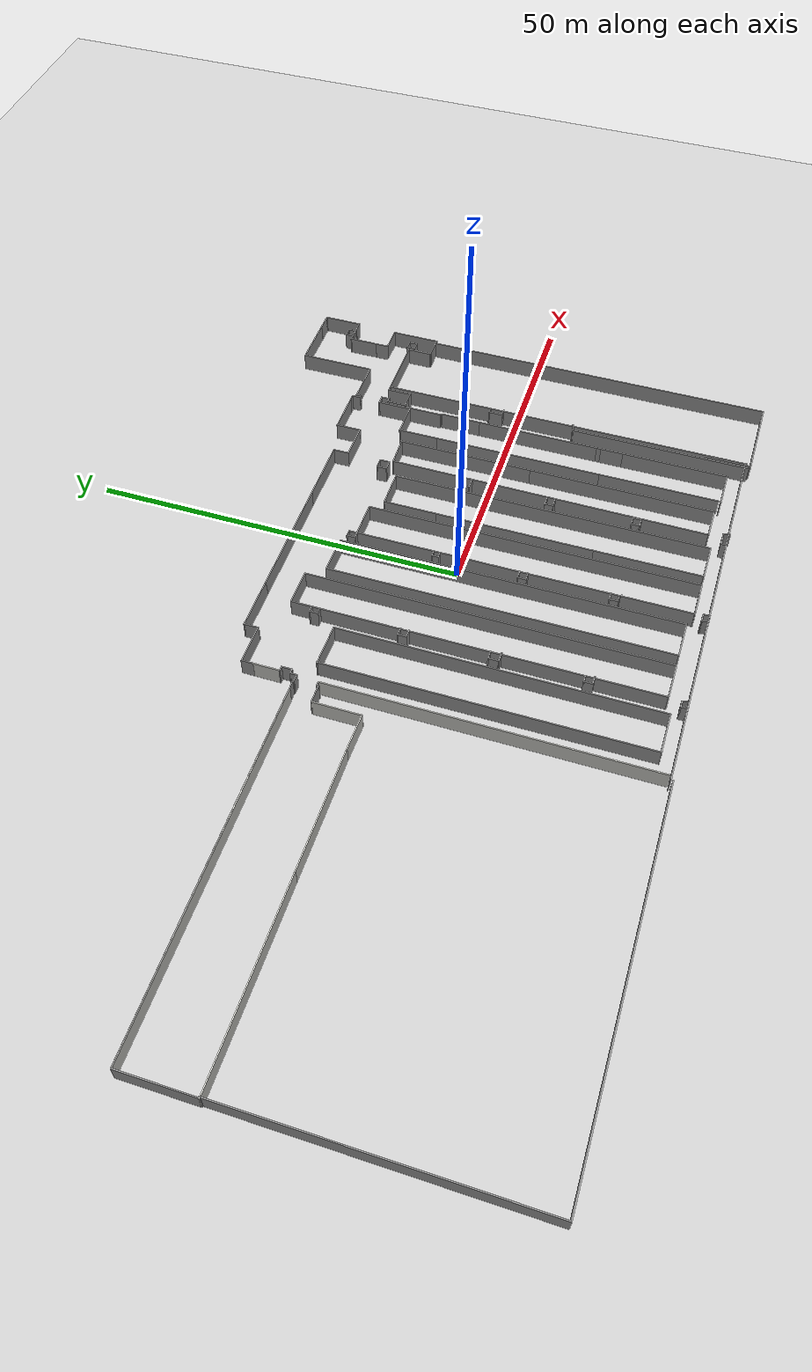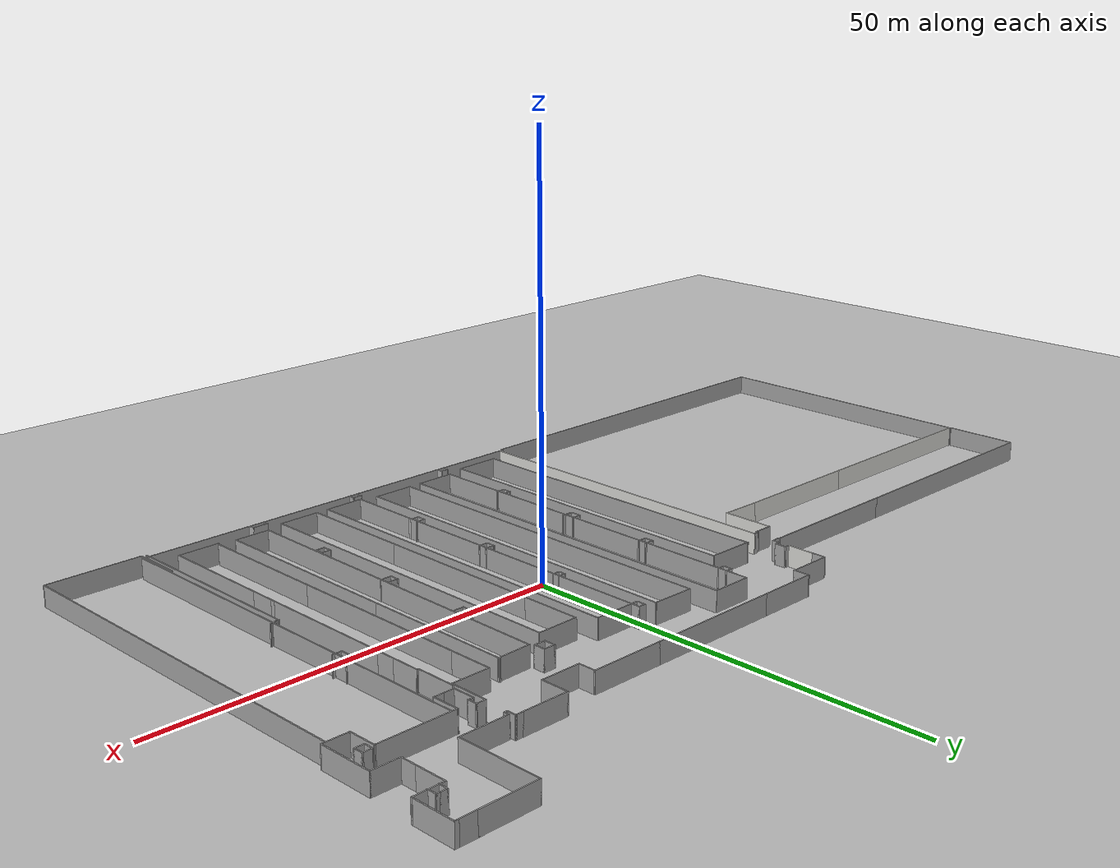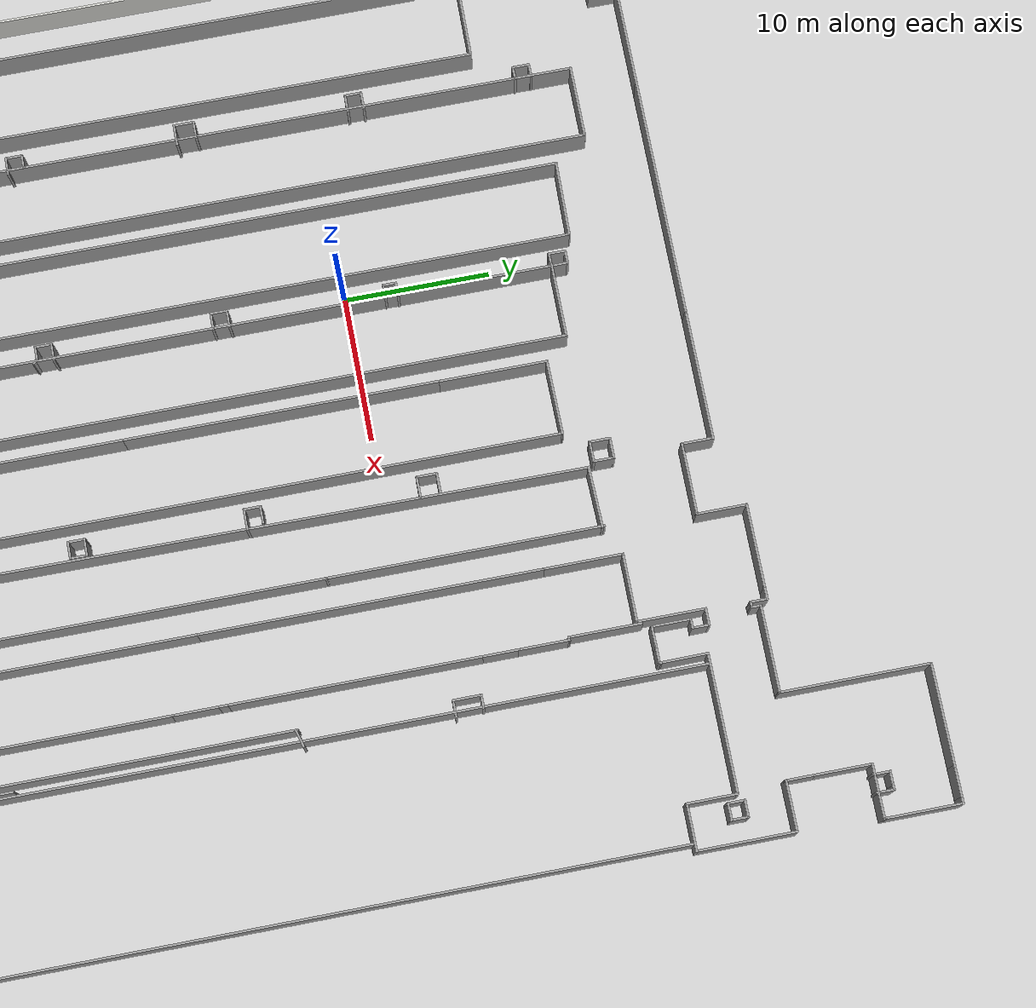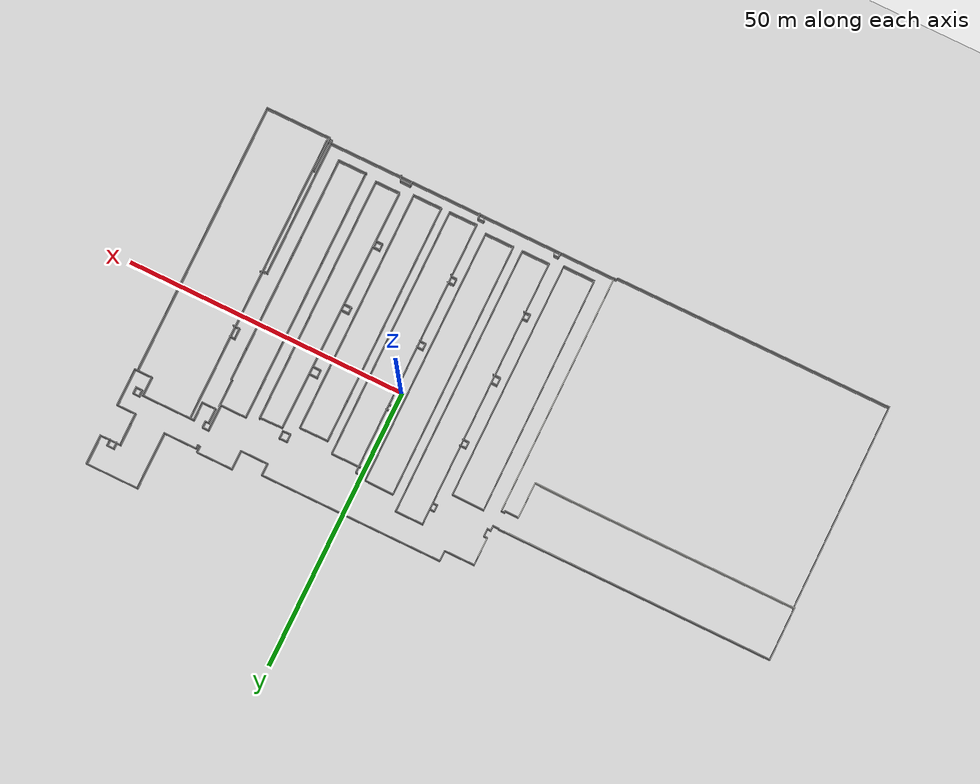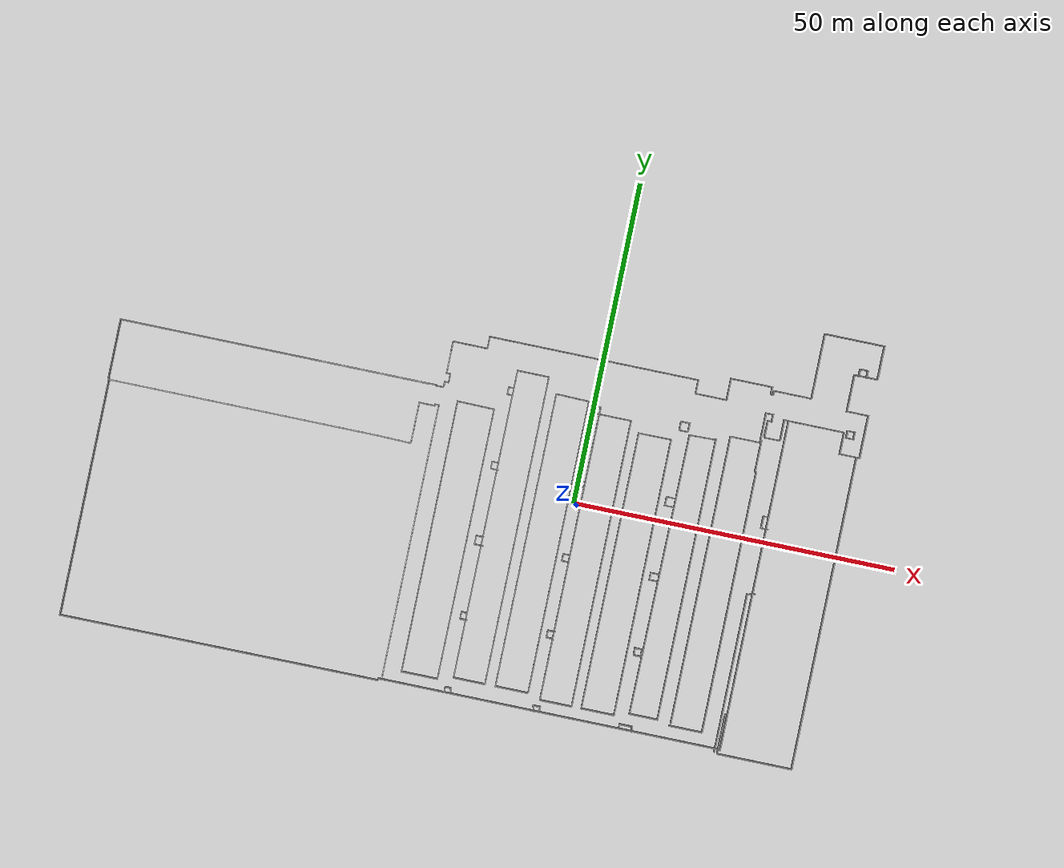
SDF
<sdf version="1.6">
 <world name="default">
  <light name="sun" type="directional">
   <pose>0 0 15 0 -0 0</pose>
   <diffuse>0.8 0.8 0.8 1</diffuse>
   <specular>0.2 0.2 0.2 1</specular>
   <attenuation>
    <range>1000</range>
    <constant>0.9</constant>
    <linear>0.01</linear>
    <quadratic>0.001</quadratic>
   </attenuation>
   <direction>-0.5 0.1 -0.9</direction>
  </light>
  <model name="ground_plane">
   <static>1</static>
   <link name="link">
    <collision name="collision">
     <geometry><plane><normal>0 0 1</normal><size>100 100</size></plane></geometry>
     <surface><friction><ode><mu>100</mu><mu2>50</mu2></ode></friction></surface>
    </collision>
    <visual name="visual">
     <transparency>1</transparency>
     <cast_shadows>0</cast_shadows>
     <geometry><plane><normal>0 0 1</normal><size>100 100</size></plane></geometry>
     <material>
      <script><uri>file://media/materials/scripts/gazebo.material</uri><name>Gazebo/Grey</name></script>
     </material>
    </visual>
   </link>
  </model>
  <gravity>0 0 -9.8</gravity>
  <magnetic_field>6e-06 2.3e-05 -4.2e-05</magnetic_field>
  <atmosphere type="adiabatic"/>
  <physics name="default_physics" default="0" type="ode">
   <max_step_size>0.001</max_step_size>
   <real_time_factor>1</real_time_factor>
   <real_time_update_rate>1000</real_time_update_rate>
  </physics>
  <scene><ambient>0.4 0.4 0.4 1</ambient><background>0.7 0.7 0.7 1</background><shadows>1</shadows></scene>
  <spherical_coordinates>
   <surface_model>EARTH_WGS84</surface_model>
   <latitude_deg>0</latitude_deg>
   <longitude_deg>0</longitude_deg>
   <elevation>0</elevation>
   <heading_deg>0</heading_deg>
  </spherical_coordinates>
  <model name="AGV_smt">
   <pose>-16.0022 0.08637 0 0 -0 0</pose>
   <link name="Wall_0">
    <collision name="Wall_0_Collision">
     <geometry><box><size>30.75 0.15 2.5</size></box></geometry>
     <pose>0 0 1.25 0 -0 0</pose>
    </collision>
    <visual name="Wall_0_Visual">
     <pose>0 0 1.25 0 -0 0</pose>
     <geometry><box><size>30.75 0.15 2.5</size></box></geometry>
     <material>
      <script><uri>file://media/materials/scripts/gazebo.material</uri><name>Gazebo/Grey</name></script>
      <ambient>1 1 1 1</ambient>
     </material>
    </visual>
    <pose>-42.1422 13.3361 0 0 -0 0</pose>
   </link>
   <link name="Wall_1">
    <collision name="Wall_1_Collision">
     <geometry><box><size>0.15 0.15 2.5</size></box></geometry>
     <pose>0 0 1.25 0 -0 0</pose>
    </collision>
    <visual name="Wall_1_Visual">
     <pose>0 0 1.25 0 -0 0</pose>
     <geometry><box><size>0.15 0.15 2.5</size></box></geometry>
     <material>
      <script><uri>file://media/materials/scripts/gazebo.material</uri><name>Gazebo/Grey</name></script>
      <ambient>1 1 1 1</ambient>
     </material>
    </visual>
    <pose>-26.8422 13.3361 0 0 -0 0</pose>
   </link>
   <link name="Wall_101">
    <collision name="Wall_101_Collision">
     <geometry><box><size>1.25 0.15 2.5</size></box></geometry>
     <pose>0 0 1.25 0 -0 0</pose>
    </collision>
    <visual name="Wall_101_Visual">
     <pose>0 0 1.25 0 -0 0</pose>
     <geometry><box><size>1.25 0.15 2.5</size></box></geometry>
     <material>
      <script><uri>file://media/materials/scripts/gazebo.material</uri><name>Gazebo/Grey</name></script>
      <ambient>1 1 1 1</ambient>
     </material>
    </visual>
    <pose>30.186 -20.9124 0 0 -0 3.14159</pose>
   </link>
   <link name="Wall_102">
    <collision name="Wall_102_Collision">
     <geometry><box><size>1.25 0.15 2.5</size></box></geometry>
     <pose>0 0 1.25 0 -0 0</pose>
    </collision>
    <visual name="Wall_102_Visual">
     <pose>0 0 1.25 0 -0 0</pose>
     <geometry><box><size>1.25 0.15 2.5</size></box></geometry>
     <material>
      <script><uri>file://media/materials/scripts/gazebo.material</uri><name>Gazebo/Grey</name></script>
      <ambient>1 1 1 1</ambient>
     </material>
    </visual>
    <pose>29.636 -20.3624 0 0 -0 1.5708</pose>
   </link>
   <link name="Wall_103">
    <collision name="Wall_103_Collision">
     <geometry><box><size>1.25 0.15 2.5</size></box></geometry>
     <pose>0 0 1.25 0 -0 0</pose>
    </collision>
    <visual name="Wall_103_Visual">
     <pose>0 0 1.25 0 -0 0</pose>
     <geometry><box><size>1.25 0.15 2.5</size></box></geometry>
     <material>
      <script><uri>file://media/materials/scripts/gazebo.material</uri><name>Gazebo/Grey</name></script>
      <ambient>1 1 1 1</ambient>
     </material>
    </visual>
    <pose>30.186 -19.8124 0 0 -0 0</pose>
   </link>
   <link name="Wall_104">
    <collision name="Wall_104_Collision">
     <geometry><box><size>1.25 0.15 2.5</size></box></geometry>
     <pose>0 0 1.25 0 -0 0</pose>
    </collision>
    <visual name="Wall_104_Visual">
     <pose>0 0 1.25 0 -0 0</pose>
     <geometry><box><size>1.25 0.15 2.5</size></box></geometry>
     <material>
      <script><uri>file://media/materials/scripts/gazebo.material</uri><name>Gazebo/Grey</name></script>
      <ambient>1 1 1 1</ambient>
     </material>
    </visual>
    <pose>30.736 -20.3624 0 0 0 -1.5708</pose>
   </link>
   <link name="Wall_106">
    <collision name="Wall_106_Collision">
     <geometry><box><size>5.25 0.15 2.5</size></box></geometry>
     <pose>0 0 1.25 0 -0 0</pose>
    </collision>
    <visual name="Wall_106_Visual">
     <pose>0 0 1.25 0 -0 0</pose>
     <geometry><box><size>5.25 0.15 2.5</size></box></geometry>
     <material>
      <script><uri>file://media/materials/scripts/gazebo.material</uri><name>Gazebo/Grey</name></script>
      <ambient>1 1 1 1</ambient>
     </material>
    </visual>
    <pose>26.0282 -30.5244 0 0 -0 3.14159</pose>
   </link>
   <link name="Wall_107">
    <collision name="Wall_107_Collision">
     <geometry><box><size>14.5 0.15 2.5</size></box></geometry>
     <pose>0 0 1.25 0 -0 0</pose>
    </collision>
    <visual name="Wall_107_Visual">
     <pose>0 0 1.25 0 -0 0</pose>
     <geometry><box><size>14.5 0.15 2.5</size></box></geometry>
     <material>
      <script><uri>file://media/materials/scripts/gazebo.material</uri><name>Gazebo/Grey</name></script>
      <ambient>1 1 1 1</ambient>
     </material>
    </visual>
    <pose>23.4782 -23.3494 0 0 -0 1.5708</pose>
   </link>
   <link name="Wall_108">
    <collision name="Wall_108_Collision">
     <geometry><box><size>21.5 0.15 2.5</size></box></geometry>
     <pose>0 0 1.25 0 -0 0</pose>
    </collision>
    <visual name="Wall_108_Visual">
     <pose>0 0 1.25 0 -0 0</pose>
     <geometry><box><size>21.5 0.15 2.5</size></box></geometry>
     <material>
      <script><uri>file://media/materials/scripts/gazebo.material</uri><name>Gazebo/Grey</name></script>
      <ambient>1 1 1 1</ambient>
     </material>
    </visual>
    <pose>23.4782 -5.49935 0 0 -0 1.5708</pose>
   </link>
   <link name="Wall_109">
    <collision name="Wall_109_Collision">
     <geometry><box><size>0.16 0.15 2.5</size></box></geometry>
     <pose>0 0 1.25 0 -0 0</pose>
    </collision>
    <visual name="Wall_109_Visual">
     <pose>0 0 1.25 0 -0 0</pose>
     <geometry><box><size>0.16 0.15 2.5</size></box></geometry>
     <material>
      <script><uri>file://media/materials/scripts/gazebo.material</uri><name>Gazebo/Grey</name></script>
      <ambient>1 1 1 1</ambient>
     </material>
    </visual>
    <pose>23.4832 5.17565 0 0 -0 0</pose>
   </link>
   <link name="Wall_11">
    <collision name="Wall_11_Collision">
     <geometry><box><size>0.75 0.15 2.5</size></box></geometry>
     <pose>0 0 1.25 0 -0 0</pose>
    </collision>
    <visual name="Wall_11_Visual">
     <pose>0 0 1.25 0 -0 0</pose>
     <geometry><box><size>0.75 0.15 2.5</size></box></geometry>
     <material>
      <script><uri>file://media/materials/scripts/gazebo.material</uri><name>Gazebo/Grey</name></script>
      <ambient>1 1 1 1</ambient>
     </material>
    </visual>
    <pose>-6.84217 15.4361 0 0 -0 3.14159</pose>
   </link>
   <link name="Wall_110">
    <collision name="Wall_110_Collision">
     <geometry><box><size>7.38165 0.15 2.5</size></box></geometry>
     <pose>0 0 1.25 0 -0 0</pose>
    </collision>
    <visual name="Wall_110_Visual">
     <pose>0 0 1.25 0 -0 0</pose>
     <geometry><box><size>7.38165 0.15 2.5</size></box></geometry>
     <material>
      <script><uri>file://media/materials/scripts/gazebo.material</uri><name>Gazebo/Grey</name></script>
      <ambient>1 1 1 1</ambient>
     </material>
    </visual>
    <pose>23.4882 8.79147 0 0 -0 1.5708</pose>
   </link>
   <link name="Wall_111">
    <collision name="Wall_111_Collision">
     <geometry><box><size>5.20841 0.15 2.5</size></box></geometry>
     <pose>0 0 1.25 0 -0 0</pose>
    </collision>
    <visual name="Wall_111_Visual">
     <pose>0 0 1.25 0 -0 0</pose>
     <geometry><box><size>5.20841 0.15 2.5</size></box></geometry>
     <material>
      <script><uri>file://media/materials/scripts/gazebo.material</uri><name>Gazebo/Grey</name></script>
      <ambient>1 1 1 1</ambient>
     </material>
    </visual>
    <pose>26.0173 12.4536 0 0 -0 0.010491</pose>
   </link>
   <link name="Wall_112">
    <collision name="Wall_112_Collision">
     <geometry><box><size>43.1317 0.15 2.5</size></box></geometry>
     <pose>0 0 1.25 0 -0 0</pose>
    </collision>
    <visual name="Wall_112_Visual">
     <pose>0 0 1.25 0 -0 0</pose>
     <geometry><box><size>43.1317 0.15 2.5</size></box></geometry>
     <material>
      <script><uri>file://media/materials/scripts/gazebo.material</uri><name>Gazebo/Grey</name></script>
      <ambient>1 1 1 1</ambient>
     </material>
    </visual>
    <pose>28.5596 -9.03046 0 0 0 -1.57018</pose>
   </link>
   <link name="Wall_115">
    <collision name="Wall_115_Collision">
     <geometry><box><size>5.25 0.15 2.5</size></box></geometry>
     <pose>0 0 1.25 0 -0 0</pose>
    </collision>
    <visual name="Wall_115_Visual">
     <pose>0 0 1.25 0 -0 0</pose>
     <geometry><box><size>5.25 0.15 2.5</size></box></geometry>
     <material>
      <script><uri>file://media/materials/scripts/gazebo.material</uri><name>Gazebo/Grey</name></script>
      <ambient>1 1 1 1</ambient>
     </material>
    </visual>
    <pose>19.4138 14.0435 0 0 -0 0</pose>
   </link>
   <link name="Wall_116">
    <collision name="Wall_116_Collision">
     <geometry><box><size>44.7152 0.15 2.5</size></box></geometry>
     <pose>0 0 1.25 0 -0 0</pose>
    </collision>
    <visual name="Wall_116_Visual">
     <pose>0 0 1.25 0 -0 0</pose>
     <geometry><box><size>44.7152 0.15 2.5</size></box></geometry>
     <material>
      <script><uri>file://media/materials/scripts/gazebo.material</uri><name>Gazebo/Grey</name></script>
      <ambient>1 1 1 1</ambient>
     </material>
    </visual>
    <pose>21.9638 -8.23909 0 0 0 -1.5708</pose>
   </link>
   <link name="Wall_117">
    <collision name="Wall_117_Collision">
     <geometry><box><size>5.09266 0.15 2.5</size></box></geometry>
     <pose>0 0 1.25 0 -0 0</pose>
    </collision>
    <visual name="Wall_117_Visual">
     <pose>0 0 1.25 0 -0 0</pose>
     <geometry><box><size>5.09266 0.15 2.5</size></box></geometry>
     <material>
      <script><uri>file://media/materials/scripts/gazebo.material</uri><name>Gazebo/Grey</name></script>
      <ambient>1 1 1 1</ambient>
     </material>
    </visual>
    <pose>19.4925 -30.5521 0 0 0 -3.13628</pose>
   </link>
   <link name="Wall_118">
    <collision name="Wall_118_Collision">
     <geometry><box><size>44.7152 0.15 2.5</size></box></geometry>
     <pose>0 0 1.25 0 -0 0</pose>
    </collision>
    <visual name="Wall_118_Visual">
     <pose>0 0 1.25 0 -0 0</pose>
     <geometry><box><size>44.7152 0.15 2.5</size></box></geometry>
     <material>
      <script><uri>file://media/materials/scripts/gazebo.material</uri><name>Gazebo/Grey</name></script>
      <ambient>1 1 1 1</ambient>
     </material>
    </visual>
    <pose>17.0179 -8.26533 0 0 -0 1.57094</pose>
   </link>
   <link name="Wall_12">
    <collision name="Wall_12_Collision">
     <geometry><box><size>3.5 0.15 2.5</size></box></geometry>
     <pose>0 0 1.25 0 -0 0</pose>
    </collision>
    <visual name="Wall_12_Visual">
     <pose>0 0 1.25 0 -0 0</pose>
     <geometry><box><size>3.5 0.15 2.5</size></box></geometry>
     <material>
      <script><uri>file://media/materials/scripts/gazebo.material</uri><name>Gazebo/CeilingTiled</name></script>
      <ambient>1 1 1 1</ambient>
     </material>
    </visual>
    <pose>-7.14217 17.1111 0 0 -0 1.5708</pose>
   </link>
   <link name="Wall_120">
    <collision name="Wall_120_Collision">
     <geometry><box><size>1.25 0.15 2.5</size></box></geometry>
     <pose>0 0 1.25 0 -0 0</pose>
    </collision>
    <visual name="Wall_120_Visual">
     <pose>0 0 1.25 0 -0 0</pose>
     <geometry><box><size>1.25 0.15 2.5</size></box></geometry>
     <material>
      <script><uri>file://media/materials/scripts/gazebo.material</uri><name>Gazebo/Grey</name></script>
      <ambient>1 1 1 1</ambient>
     </material>
    </visual>
    <pose>17.0146 14.5673 0 0 -0 1.5708</pose>
   </link>
   <link name="Wall_121">
    <collision name="Wall_121_Collision">
     <geometry><box><size>1 0.15 2.5</size></box></geometry>
     <pose>0 0 1.25 0 -0 0</pose>
    </collision>
    <visual name="Wall_121_Visual">
     <pose>0 0 1.25 0 -0 0</pose>
     <geometry><box><size>1 0.15 2.5</size></box></geometry>
     <material>
      <script><uri>file://media/materials/scripts/gazebo.material</uri><name>Gazebo/Grey</name></script>
      <ambient>1 1 1 1</ambient>
     </material>
    </visual>
    <pose>16.5896 15.1173 0 0 -0 3.14159</pose>
   </link>
   <link name="Wall_122">
    <collision name="Wall_122_Collision">
     <geometry><box><size>1.25 0.15 2.5</size></box></geometry>
     <pose>0 0 1.25 0 -0 0</pose>
    </collision>
    <visual name="Wall_122_Visual">
     <pose>0 0 1.25 0 -0 0</pose>
     <geometry><box><size>1.25 0.15 2.5</size></box></geometry>
     <material>
      <script><uri>file://media/materials/scripts/gazebo.material</uri><name>Gazebo/Grey</name></script>
      <ambient>1 1 1 1</ambient>
     </material>
    </visual>
    <pose>16.1646 14.5673 0 0 0 -1.5708</pose>
   </link>
   <link name="Wall_123">
    <collision name="Wall_123_Collision">
     <geometry><box><size>1 0.15 2.5</size></box></geometry>
     <pose>0 0 1.25 0 -0 0</pose>
    </collision>
    <visual name="Wall_123_Visual">
     <pose>0 0 1.25 0 -0 0</pose>
     <geometry><box><size>1 0.15 2.5</size></box></geometry>
     <material>
      <script><uri>file://media/materials/scripts/gazebo.material</uri><name>Gazebo/Grey</name></script>
      <ambient>1 1 1 1</ambient>
     </material>
    </visual>
    <pose>16.5896 14.0173 0 0 -0 0</pose>
   </link>
   <link name="Wall_125">
    <collision name="Wall_125_Collision">
     <geometry><box><size>1 0.15 2.5</size></box></geometry>
     <pose>0 0 1.25 0 -0 0</pose>
    </collision>
    <visual name="Wall_125_Visual">
     <pose>0 0 1.25 0 -0 0</pose>
     <geometry><box><size>1 0.15 2.5</size></box></geometry>
     <material>
      <script><uri>file://media/materials/scripts/gazebo.material</uri><name>Gazebo/Grey</name></script>
      <ambient>1 1 1 1</ambient>
     </material>
    </visual>
    <pose>16.6409 3.50389 0 0 -0 3.14159</pose>
   </link>
   <link name="Wall_126">
    <collision name="Wall_126_Collision">
     <geometry><box><size>1 0.15 2.5</size></box></geometry>
     <pose>0 0 1.25 0 -0 0</pose>
    </collision>
    <visual name="Wall_126_Visual">
     <pose>0 0 1.25 0 -0 0</pose>
     <geometry><box><size>1 0.15 2.5</size></box></geometry>
     <material>
      <script><uri>file://media/materials/scripts/gazebo.material</uri><name>Gazebo/Grey</name></script>
      <ambient>1 1 1 1</ambient>
     </material>
    </visual>
    <pose>16.2159 3.07889 0 0 0 -1.5708</pose>
   </link>
   <link name="Wall_127">
    <collision name="Wall_127_Collision">
     <geometry><box><size>1 0.15 2.5</size></box></geometry>
     <pose>0 0 1.25 0 -0 0</pose>
    </collision>
    <visual name="Wall_127_Visual">
     <pose>0 0 1.25 0 -0 0</pose>
     <geometry><box><size>1 0.15 2.5</size></box></geometry>
     <material>
      <script><uri>file://media/materials/scripts/gazebo.material</uri><name>Gazebo/Grey</name></script>
      <ambient>1 1 1 1</ambient>
     </material>
    </visual>
    <pose>16.6409 2.65389 0 0 -0 0</pose>
   </link>
   <link name="Wall_129">
    <collision name="Wall_129_Collision">
     <geometry><box><size>1.25 0.15 2.5</size></box></geometry>
     <pose>0 0 1.25 0 -0 0</pose>
    </collision>
    <visual name="Wall_129_Visual">
     <pose>0 0 1.25 0 -0 0</pose>
     <geometry><box><size>1.25 0.15 2.5</size></box></geometry>
     <material>
      <script><uri>file://media/materials/scripts/gazebo.material</uri><name>Gazebo/Grey</name></script>
      <ambient>1 1 1 1</ambient>
     </material>
    </visual>
    <pose>16.5293 -7.97039 0 0 -0 3.14159</pose>
   </link>
   <link name="Wall_130">
    <collision name="Wall_130_Collision">
     <geometry><box><size>1.25 0.15 2.5</size></box></geometry>
     <pose>0 0 1.25 0 -0 0</pose>
    </collision>
    <visual name="Wall_130_Visual">
     <pose>0 0 1.25 0 -0 0</pose>
     <geometry><box><size>1.25 0.15 2.5</size></box></geometry>
     <material>
      <script><uri>file://media/materials/scripts/gazebo.material</uri><name>Gazebo/Grey</name></script>
      <ambient>1 1 1 1</ambient>
     </material>
    </visual>
    <pose>15.9793 -8.52039 0 0 0 -1.5708</pose>
   </link>
   <link name="Wall_131">
    <collision name="Wall_131_Collision">
     <geometry><box><size>1.25 0.15 2.5</size></box></geometry>
     <pose>0 0 1.25 0 -0 0</pose>
    </collision>
    <visual name="Wall_131_Visual">
     <pose>0 0 1.25 0 -0 0</pose>
     <geometry><box><size>1.25 0.15 2.5</size></box></geometry>
     <material>
      <script><uri>file://media/materials/scripts/gazebo.material</uri><name>Gazebo/Grey</name></script>
      <ambient>1 1 1 1</ambient>
     </material>
    </visual>
    <pose>16.5293 -9.07039 0 0 -0 0</pose>
   </link>
   <link name="Wall_133">
    <collision name="Wall_133_Collision">
     <geometry><box><size>1.25 0.15 2.5</size></box></geometry>
     <pose>0 0 1.25 0 -0 0</pose>
    </collision>
    <visual name="Wall_133_Visual">
     <pose>0 0 1.25 0 -0 0</pose>
     <geometry><box><size>1.25 0.15 2.5</size></box></geometry>
     <material>
      <script><uri>file://media/materials/scripts/gazebo.material</uri><name>Gazebo/Grey</name></script>
      <ambient>1 1 1 1</ambient>
     </material>
    </visual>
    <pose>16.606 -19.8824 0 0 -0 3.14159</pose>
   </link>
   <link name="Wall_134">
    <collision name="Wall_134_Collision">
     <geometry><box><size>1.25 0.15 2.5</size></box></geometry>
     <pose>0 0 1.25 0 -0 0</pose>
    </collision>
    <visual name="Wall_134_Visual">
     <pose>0 0 1.25 0 -0 0</pose>
     <geometry><box><size>1.25 0.15 2.5</size></box></geometry>
     <material>
      <script><uri>file://media/materials/scripts/gazebo.material</uri><name>Gazebo/Grey</name></script>
      <ambient>1 1 1 1</ambient>
     </material>
    </visual>
    <pose>16.056 -20.4324 0 0 0 -1.5708</pose>
   </link>
   <link name="Wall_135">
    <collision name="Wall_135_Collision">
     <geometry><box><size>1 0.15 2.5</size></box></geometry>
     <pose>0 0 1.25 0 -0 0</pose>
    </collision>
    <visual name="Wall_135_Visual">
     <pose>0 0 1.25 0 -0 0</pose>
     <geometry><box><size>1 0.15 2.5</size></box></geometry>
     <material>
      <script><uri>file://media/materials/scripts/gazebo.material</uri><name>Gazebo/Grey</name></script>
      <ambient>1 1 1 1</ambient>
     </material>
    </visual>
    <pose>16.481 -20.9824 0 0 -0 0</pose>
   </link>
   <link name="Wall_136">
    <collision name="Wall_136_Collision">
     <geometry><box><size>0.5 0.15 2.5</size></box></geometry>
     <pose>0 0 1.25 0 -0 0</pose>
    </collision>
    <visual name="Wall_136_Visual">
     <pose>0 0 1.25 0 -0 0</pose>
     <geometry><box><size>0.5 0.15 2.5</size></box></geometry>
     <material>
      <script><uri>file://media/materials/scripts/gazebo.material</uri><name>Gazebo/Grey</name></script>
      <ambient>1 1 1 1</ambient>
     </material>
    </visual>
    <pose>17.0298 -21.1061 0 0 0 -0.785398</pose>
   </link>
   <link name="Wall_138">
    <collision name="Wall_138_Collision">
     <geometry><box><size>5.24416 0.15 2.5</size></box></geometry>
     <pose>0 0 1.25 0 -0 0</pose>
    </collision>
    <visual name="Wall_138_Visual">
     <pose>0 0 1.25 0 -0 0</pose>
     <geometry><box><size>5.24416 0.15 2.5</size></box></geometry>
     <material>
      <script><uri>file://media/materials/scripts/gazebo.material</uri><name>Gazebo/Grey</name></script>
      <ambient>1 1 1 1</ambient>
     </material>
    </visual>
    <pose>12.5085 15.6745 0 0 0 -0.02094</pose>
   </link>
   <link name="Wall_139">
    <collision name="Wall_139_Collision">
     <geometry><box><size>45.6529 0.15 2.5</size></box></geometry>
     <pose>0 0 1.25 0 -0 0</pose>
    </collision>
    <visual name="Wall_139_Visual">
     <pose>0 0 1.25 0 -0 0</pose>
     <geometry><box><size>45.6529 0.15 2.5</size></box></geometry>
     <material>
      <script><uri>file://media/materials/scripts/gazebo.material</uri><name>Gazebo/Grey</name></script>
      <ambient>1 1 1 1</ambient>
     </material>
    </visual>
    <pose>15.0467 -7.13023 0 0 0 -1.57116</pose>
   </link>
   <link name="Wall_14">
    <collision name="Wall_14_Collision">
     <geometry><box><size>1.75 0.15 2.5</size></box></geometry>
     <pose>0 0 1.25 0 -0 0</pose>
    </collision>
    <visual name="Wall_14_Visual">
     <pose>0 0 1.25 0 -0 0</pose>
     <geometry><box><size>1.75 0.15 2.5</size></box></geometry>
     <material>
      <script><uri>file://media/materials/scripts/gazebo.material</uri><name>Gazebo/Grey</name></script>
      <ambient>1 1 1 1</ambient>
     </material>
    </visual>
    <pose>-7.14217 19.5861 0 0 -0 1.5708</pose>
   </link>
   <link name="Wall_140">
    <collision name="Wall_140_Collision">
     <geometry><box><size>5.25 0.15 2.5</size></box></geometry>
     <pose>0 0 1.25 0 -0 0</pose>
    </collision>
    <visual name="Wall_140_Visual">
     <pose>0 0 1.25 0 -0 0</pose>
     <geometry><box><size>5.25 0.15 2.5</size></box></geometry>
     <material>
      <script><uri>file://media/materials/scripts/gazebo.material</uri><name>Gazebo/Grey</name></script>
      <ambient>1 1 1 1</ambient>
     </material>
    </visual>
    <pose>12.4884 -29.8817 0 0 -0 3.14159</pose>
   </link>
   <link name="Wall_141">
    <collision name="Wall_141_Collision">
     <geometry><box><size>45.75 0.15 2.5</size></box></geometry>
     <pose>0 0 1.25 0 -0 0</pose>
    </collision>
    <visual name="Wall_141_Visual">
     <pose>0 0 1.25 0 -0 0</pose>
     <geometry><box><size>45.75 0.15 2.5</size></box></geometry>
     <material>
      <script><uri>file://media/materials/scripts/gazebo.material</uri><name>Gazebo/Grey</name></script>
      <ambient>1 1 1 1</ambient>
     </material>
    </visual>
    <pose>9.93842 -7.07681 0 0 -0 1.5708</pose>
   </link>
   <link name="Wall_143">
    <collision name="Wall_143_Collision">
     <geometry><box><size>5.0499 0.15 2.5</size></box></geometry>
     <pose>0 0 1.25 0 -0 0</pose>
    </collision>
    <visual name="Wall_143_Visual">
     <pose>0 0 1.25 0 -0 0</pose>
     <geometry><box><size>5.0499 0.15 2.5</size></box></geometry>
     <material>
      <script><uri>file://media/materials/scripts/gazebo.material</uri><name>Gazebo/Grey</name></script>
      <ambient>1 1 1 1</ambient>
     </material>
    </visual>
    <pose>5.86336 18.025 0 0 -0 0</pose>
   </link>
   <link name="Wall_144">
    <collision name="Wall_144_Collision">
     <geometry><box><size>48.0563 0.15 2.5</size></box></geometry>
     <pose>0 0 1.25 0 -0 0</pose>
    </collision>
    <visual name="Wall_144_Visual">
     <pose>0 0 1.25 0 -0 0</pose>
     <geometry><box><size>48.0563 0.15 2.5</size></box></geometry>
     <material>
      <script><uri>file://media/materials/scripts/gazebo.material</uri><name>Gazebo/Grey</name></script>
      <ambient>1 1 1 1</ambient>
     </material>
    </visual>
    <pose>8.30876 -5.94292 0 0 0 -1.57099</pose>
   </link>
   <link name="Wall_145">
    <collision name="Wall_145_Collision">
     <geometry><box><size>5.0499 0.15 2.5</size></box></geometry>
     <pose>0 0 1.25 0 -0 0</pose>
    </collision>
    <visual name="Wall_145_Visual">
     <pose>0 0 1.25 0 -0 0</pose>
     <geometry><box><size>5.0499 0.15 2.5</size></box></geometry>
     <material>
      <script><uri>file://media/materials/scripts/gazebo.material</uri><name>Gazebo/Grey</name></script>
      <ambient>1 1 1 1</ambient>
     </material>
    </visual>
    <pose>5.85426 -29.9016 0 0 -0 3.14159</pose>
   </link>
   <link name="Wall_146">
    <collision name="Wall_146_Collision">
     <geometry><box><size>48.0563 0.15 2.5</size></box></geometry>
     <pose>0 0 1.25 0 -0 0</pose>
    </collision>
    <visual name="Wall_146_Visual">
     <pose>0 0 1.25 0 -0 0</pose>
     <geometry><box><size>48.0563 0.15 2.5</size></box></geometry>
     <material>
      <script><uri>file://media/materials/scripts/gazebo.material</uri><name>Gazebo/Grey</name></script>
      <ambient>1 1 1 1</ambient>
     </material>
    </visual>
    <pose>3.40886 -5.94292 0 0 -0 1.57061</pose>
   </link>
   <link name="Wall_148">
    <collision name="Wall_148_Collision">
     <geometry><box><size>1 0.15 2.5</size></box></geometry>
     <pose>0 0 1.25 0 -0 0</pose>
    </collision>
    <visual name="Wall_148_Visual">
     <pose>0 0 1.25 0 -0 0</pose>
     <geometry><box><size>1 0.15 2.5</size></box></geometry>
     <material>
      <script><uri>file://media/materials/scripts/gazebo.material</uri><name>Gazebo/Grey</name></script>
      <ambient>1 1 1 1</ambient>
     </material>
    </visual>
    <pose>3.04093 15.2638 0 0 -0 3.14159</pose>
   </link>
   <link name="Wall_149">
    <collision name="Wall_149_Collision">
     <geometry><box><size>1.25 0.15 2.5</size></box></geometry>
     <pose>0 0 1.25 0 -0 0</pose>
    </collision>
    <visual name="Wall_149_Visual">
     <pose>0 0 1.25 0 -0 0</pose>
     <geometry><box><size>1.25 0.15 2.5</size></box></geometry>
     <material>
      <script><uri>file://media/materials/scripts/gazebo.material</uri><name>Gazebo/Grey</name></script>
      <ambient>1 1 1 1</ambient>
     </material>
    </visual>
    <pose>2.61593 14.7138 0 0 0 -1.5708</pose>
   </link>
   <link name="Wall_15">
    <collision name="Wall_15_Collision">
     <geometry><box><size>5.5 0.15 2.5</size></box></geometry>
     <pose>0 0 1.25 0 -0 0</pose>
    </collision>
    <visual name="Wall_15_Visual">
     <pose>0 0 1.25 0 -0 0</pose>
     <geometry><box><size>5.5 0.15 2.5</size></box></geometry>
     <material>
      <script><uri>file://media/materials/scripts/gazebo.material</uri><name>Gazebo/Grey</name></script>
      <ambient>1 1 1 1</ambient>
     </material>
    </visual>
    <pose>-4.46717 20.3861 0 0 -0 0</pose>
   </link>
   <link name="Wall_150">
    <collision name="Wall_150_Collision">
     <geometry><box><size>1 0.15 2.5</size></box></geometry>
     <pose>0 0 1.25 0 -0 0</pose>
    </collision>
    <visual name="Wall_150_Visual">
     <pose>0 0 1.25 0 -0 0</pose>
     <geometry><box><size>1 0.15 2.5</size></box></geometry>
     <material>
      <script><uri>file://media/materials/scripts/gazebo.material</uri><name>Gazebo/Grey</name></script>
      <ambient>1 1 1 1</ambient>
     </material>
    </visual>
    <pose>3.04093 14.1638 0 0 -0 0</pose>
   </link>
   <link name="Wall_152">
    <collision name="Wall_152_Collision">
     <geometry><box><size>1.25 0.15 2.5</size></box></geometry>
     <pose>0 0 1.25 0 -0 0</pose>
    </collision>
    <visual name="Wall_152_Visual">
     <pose>0 0 1.25 0 -0 0</pose>
     <geometry><box><size>1.25 0.15 2.5</size></box></geometry>
     <material>
      <script><uri>file://media/materials/scripts/gazebo.material</uri><name>Gazebo/Grey</name></script>
      <ambient>1 1 1 1</ambient>
     </material>
    </visual>
    <pose>3.00565 3.62322 0 0 -0 3.14159</pose>
   </link>
   <link name="Wall_153">
    <collision name="Wall_153_Collision">
     <geometry><box><size>1.25 0.15 2.5</size></box></geometry>
     <pose>0 0 1.25 0 -0 0</pose>
    </collision>
    <visual name="Wall_153_Visual">
     <pose>0 0 1.25 0 -0 0</pose>
     <geometry><box><size>1.25 0.15 2.5</size></box></geometry>
     <material>
      <script><uri>file://media/materials/scripts/gazebo.material</uri><name>Gazebo/Grey</name></script>
      <ambient>1 1 1 1</ambient>
     </material>
    </visual>
    <pose>2.45565 3.07322 0 0 0 -1.5708</pose>
   </link>
   <link name="Wall_154">
    <collision name="Wall_154_Collision">
     <geometry><box><size>1.25 0.15 2.5</size></box></geometry>
     <pose>0 0 1.25 0 -0 0</pose>
    </collision>
    <visual name="Wall_154_Visual">
     <pose>0 0 1.25 0 -0 0</pose>
     <geometry><box><size>1.25 0.15 2.5</size></box></geometry>
     <material>
      <script><uri>file://media/materials/scripts/gazebo.material</uri><name>Gazebo/Grey</name></script>
      <ambient>1 1 1 1</ambient>
     </material>
    </visual>
    <pose>3.00565 2.52322 0 0 -0 0</pose>
   </link>
   <link name="Wall_156">
    <collision name="Wall_156_Collision">
     <geometry><box><size>1.25 0.15 2.5</size></box></geometry>
     <pose>0 0 1.25 0 -0 0</pose>
    </collision>
    <visual name="Wall_156_Visual">
     <pose>0 0 1.25 0 -0 0</pose>
     <geometry><box><size>1.25 0.15 2.5</size></box></geometry>
     <material>
      <script><uri>file://media/materials/scripts/gazebo.material</uri><name>Gazebo/Grey</name></script>
      <ambient>1 1 1 1</ambient>
     </material>
    </visual>
    <pose>2.927 -7.94972 0 0 -0 3.14159</pose>
   </link>
   <link name="Wall_157">
    <collision name="Wall_157_Collision">
     <geometry><box><size>1.5 0.15 2.5</size></box></geometry>
     <pose>0 0 1.25 0 -0 0</pose>
    </collision>
    <visual name="Wall_157_Visual">
     <pose>0 0 1.25 0 -0 0</pose>
     <geometry><box><size>1.5 0.15 2.5</size></box></geometry>
     <material>
      <script><uri>file://media/materials/scripts/gazebo.material</uri><name>Gazebo/Grey</name></script>
      <ambient>1 1 1 1</ambient>
     </material>
    </visual>
    <pose>2.377 -8.62472 0 0 0 -1.5708</pose>
   </link>
   <link name="Wall_158">
    <collision name="Wall_158_Collision">
     <geometry><box><size>1.5 0.15 2.5</size></box></geometry>
     <pose>0 0 1.25 0 -0 0</pose>
    </collision>
    <visual name="Wall_158_Visual">
     <pose>0 0 1.25 0 -0 0</pose>
     <geometry><box><size>1.5 0.15 2.5</size></box></geometry>
     <material>
      <script><uri>file://media/materials/scripts/gazebo.material</uri><name>Gazebo/Grey</name></script>
      <ambient>1 1 1 1</ambient>
     </material>
    </visual>
    <pose>3.052 -9.29972 0 0 -0 0</pose>
   </link>
   <link name="Wall_16">
    <collision name="Wall_16_Collision">
     <geometry><box><size>2 0.15 2.5</size></box></geometry>
     <pose>0 0 1.25 0 -0 0</pose>
    </collision>
    <visual name="Wall_16_Visual">
     <pose>0 0 1.25 0 -0 0</pose>
     <geometry><box><size>2 0.15 2.5</size></box></geometry>
     <material>
      <script><uri>file://media/materials/scripts/gazebo.material</uri><name>Gazebo/Grey</name></script>
      <ambient>1 1 1 1</ambient>
     </material>
    </visual>
    <pose>-1.79217 21.3111 0 0 -0 1.5708</pose>
   </link>
   <link name="Wall_160">
    <collision name="Wall_160_Collision">
     <geometry><box><size>1 0.15 2.5</size></box></geometry>
     <pose>0 0 1.25 0 -0 0</pose>
    </collision>
    <visual name="Wall_160_Visual">
     <pose>0 0 1.25 0 -0 0</pose>
     <geometry><box><size>1 0.15 2.5</size></box></geometry>
     <material>
      <script><uri>file://media/materials/scripts/gazebo.material</uri><name>Gazebo/Grey</name></script>
      <ambient>1 1 1 1</ambient>
     </material>
    </visual>
    <pose>2.95939 -19.7967 0 0 -0 3.14159</pose>
   </link>
   <link name="Wall_161">
    <collision name="Wall_161_Collision">
     <geometry><box><size>1.25 0.15 2.5</size></box></geometry>
     <pose>0 0 1.25 0 -0 0</pose>
    </collision>
    <visual name="Wall_161_Visual">
     <pose>0 0 1.25 0 -0 0</pose>
     <geometry><box><size>1.25 0.15 2.5</size></box></geometry>
     <material>
      <script><uri>file://media/materials/scripts/gazebo.material</uri><name>Gazebo/Grey</name></script>
      <ambient>1 1 1 1</ambient>
     </material>
    </visual>
    <pose>2.53438 -20.3467 0 0 0 -1.5708</pose>
   </link>
   <link name="Wall_162">
    <collision name="Wall_162_Collision">
     <geometry><box><size>1.25 0.15 2.5</size></box></geometry>
     <pose>0 0 1.25 0 -0 0</pose>
    </collision>
    <visual name="Wall_162_Visual">
     <pose>0 0 1.25 0 -0 0</pose>
     <geometry><box><size>1.25 0.15 2.5</size></box></geometry>
     <material>
      <script><uri>file://media/materials/scripts/gazebo.material</uri><name>Gazebo/Grey</name></script>
      <ambient>1 1 1 1</ambient>
     </material>
    </visual>
    <pose>3.08439 -20.8967 0 0 -0 0</pose>
   </link>
   <link name="Wall_166">
    <collision name="Wall_166_Collision">
     <geometry><box><size>5.86862 0.15 2.5</size></box></geometry>
     <pose>0 0 1.25 0 -0 0</pose>
    </collision>
    <visual name="Wall_166_Visual">
     <pose>0 0 1.25 0 -0 0</pose>
     <geometry><box><size>5.86862 0.15 2.5</size></box></geometry>
     <material>
      <script><uri>file://media/materials/scripts/gazebo.material</uri><name>Gazebo/Grey</name></script>
      <ambient>1 1 1 1</ambient>
     </material>
    </visual>
    <pose>-1.7875 11.534 0 0 0 -0.012572</pose>
   </link>
   <link name="Wall_167">
    <collision name="Wall_167_Collision">
     <geometry><box><size>42.2453 0.15 2.5</size></box></geometry>
     <pose>0 0 1.25 0 -0 0</pose>
    </collision>
    <visual name="Wall_167_Visual">
     <pose>0 0 1.25 0 -0 0</pose>
     <geometry><box><size>42.2453 0.15 2.5</size></box></geometry>
     <material>
      <script><uri>file://media/materials/scripts/gazebo.material</uri><name>Gazebo/Grey</name></script>
      <ambient>1 1 1 1</ambient>
     </material>
    </visual>
    <pose>1.06981 -9.54955 0 0 0 -1.57277</pose>
   </link>
   <link name="Wall_168">
    <collision name="Wall_168_Collision">
     <geometry><box><size>5.75 0.15 2.5</size></box></geometry>
     <pose>0 0 1.25 0 -0 0</pose>
    </collision>
    <visual name="Wall_168_Visual">
     <pose>0 0 1.25 0 -0 0</pose>
     <geometry><box><size>5.75 0.15 2.5</size></box></geometry>
     <material>
      <script><uri>file://media/materials/scripts/gazebo.material</uri><name>Gazebo/Grey</name></script>
      <ambient>1 1 1 1</ambient>
     </material>
    </visual>
    <pose>-1.77165 -30.5972 0 0 -0 3.14159</pose>
   </link>
   <link name="Wall_169">
    <collision name="Wall_169_Collision">
     <geometry><box><size>42.3582 0.15 2.5</size></box></geometry>
     <pose>0 0 1.25 0 -0 0</pose>
    </collision>
    <visual name="Wall_169_Visual">
     <pose>0 0 1.25 0 -0 0</pose>
     <geometry><box><size>42.3582 0.15 2.5</size></box></geometry>
     <material>
      <script><uri>file://media/materials/scripts/gazebo.material</uri><name>Gazebo/Grey</name></script>
      <ambient>1 1 1 1</ambient>
     </material>
    </visual>
    <pose>-4.59598 -9.52309 0 0 -0 1.57195</pose>
   </link>
   <link name="Wall_17">
    <collision name="Wall_17_Collision">
     <geometry><box><size>7.25 0.15 2.5</size></box></geometry>
     <pose>0 0 1.25 0 -0 0</pose>
    </collision>
    <visual name="Wall_17_Visual">
     <pose>0 0 1.25 0 -0 0</pose>
     <geometry><box><size>7.25 0.15 2.5</size></box></geometry>
     <material>
      <script><uri>file://media/materials/scripts/gazebo.material</uri><name>Gazebo/Grey</name></script>
      <ambient>1 1 1 1</ambient>
     </material>
    </visual>
    <pose>1.75783 22.2361 0 0 -0 0</pose>
   </link>
   <link name="Wall_171">
    <collision name="Wall_171_Collision">
     <geometry><box><size>53.5 0.15 2.5</size></box></geometry>
     <pose>0 0 1.25 0 -0 0</pose>
    </collision>
    <visual name="Wall_171_Visual">
     <pose>0 0 1.25 0 -0 0</pose>
     <geometry><box><size>53.5 0.15 2.5</size></box></geometry>
     <material>
      <script><uri>file://media/materials/scripts/gazebo.material</uri><name>Gazebo/Grey</name></script>
      <ambient>1 1 1 1</ambient>
     </material>
    </visual>
    <pose>18.8532 -32.3575 0 0 -0 0</pose>
   </link>
   <link name="Wall_172">
    <collision name="Wall_172_Collision">
     <geometry><box><size>51.4198 0.15 2.5</size></box></geometry>
     <pose>0 0 1.25 0 -0 0</pose>
    </collision>
    <visual name="Wall_172_Visual">
     <pose>0 0 1.25 0 -0 0</pose>
     <geometry><box><size>51.4198 0.15 2.5</size></box></geometry>
     <material>
      <script><uri>file://media/materials/scripts/gazebo.material</uri><name>Gazebo/Grey</name></script>
      <ambient>1 1 1 1</ambient>
     </material>
    </visual>
    <pose>45.5282 -6.82754 0 0 -0 1.5708</pose>
   </link>
   <link name="Wall_174">
    <collision name="Wall_174_Collision">
     <geometry><box><size>1.25 0.15 2.5</size></box></geometry>
     <pose>0 0 1.25 0 -0 0</pose>
    </collision>
    <visual name="Wall_174_Visual">
     <pose>0 0 1.25 0 -0 0</pose>
     <geometry><box><size>1.25 0.15 2.5</size></box></geometry>
     <material>
      <script><uri>file://media/materials/scripts/gazebo.material</uri><name>Gazebo/Grey</name></script>
      <ambient>1 1 1 1</ambient>
     </material>
    </visual>
    <pose>54.69 18.7491 0 0 0 -1.5708</pose>
   </link>
   <link name="Wall_175">
    <collision name="Wall_175_Collision">
     <geometry><box><size>1.25 0.15 2.5</size></box></geometry>
     <pose>0 0 1.25 0 -0 0</pose>
    </collision>
    <visual name="Wall_175_Visual">
     <pose>0 0 1.25 0 -0 0</pose>
     <geometry><box><size>1.25 0.15 2.5</size></box></geometry>
     <material>
      <script><uri>file://media/materials/scripts/gazebo.material</uri><name>Gazebo/Grey</name></script>
      <ambient>1 1 1 1</ambient>
     </material>
    </visual>
    <pose>55.2401 18.1991 0 0 -0 0</pose>
   </link>
   <link name="Wall_176">
    <collision name="Wall_176_Collision">
     <geometry><box><size>1.25 0.15 2.5</size></box></geometry>
     <pose>0 0 1.25 0 -0 0</pose>
    </collision>
    <visual name="Wall_176_Visual">
     <pose>0 0 1.25 0 -0 0</pose>
     <geometry><box><size>1.25 0.15 2.5</size></box></geometry>
     <material>
      <script><uri>file://media/materials/scripts/gazebo.material</uri><name>Gazebo/Grey</name></script>
      <ambient>1 1 1 1</ambient>
     </material>
    </visual>
    <pose>55.7901 18.7491 0 0 -0 1.5708</pose>
   </link>
   <link name="Wall_177">
    <collision name="Wall_177_Collision">
     <geometry><box><size>1.25 0.15 2.5</size></box></geometry>
     <pose>0 0 1.25 0 -0 0</pose>
    </collision>
    <visual name="Wall_177_Visual">
     <pose>0 0 1.25 0 -0 0</pose>
     <geometry><box><size>1.25 0.15 2.5</size></box></geometry>
     <material>
      <script><uri>file://media/materials/scripts/gazebo.material</uri><name>Gazebo/Grey</name></script>
      <ambient>1 1 1 1</ambient>
     </material>
    </visual>
    <pose>55.2401 19.2991 0 0 -0 3.14159</pose>
   </link>
   <link name="Wall_179">
    <collision name="Wall_179_Collision">
     <geometry><box><size>1.25 0.15 2.5</size></box></geometry>
     <pose>0 0 1.25 0 -0 0</pose>
    </collision>
    <visual name="Wall_179_Visual">
     <pose>0 0 1.25 0 -0 0</pose>
     <geometry><box><size>1.25 0.15 2.5</size></box></geometry>
     <material>
      <script><uri>file://media/materials/scripts/gazebo.material</uri><name>Gazebo/Grey</name></script>
      <ambient>1 1 1 1</ambient>
     </material>
    </visual>
    <pose>54.6433 28.3539 0 0 -0 1.5708</pose>
   </link>
   <link name="Wall_180">
    <collision name="Wall_180_Collision">
     <geometry><box><size>1 0.15 2.5</size></box></geometry>
     <pose>0 0 1.25 0 -0 0</pose>
    </collision>
    <visual name="Wall_180_Visual">
     <pose>0 0 1.25 0 -0 0</pose>
     <geometry><box><size>1 0.15 2.5</size></box></geometry>
     <material>
      <script><uri>file://media/materials/scripts/gazebo.material</uri><name>Gazebo/Grey</name></script>
      <ambient>1 1 1 1</ambient>
     </material>
    </visual>
    <pose>55.0683 28.9039 0 0 -0 0</pose>
   </link>
   <link name="Wall_181">
    <collision name="Wall_181_Collision">
     <geometry><box><size>0.5 0.15 2.5</size></box></geometry>
     <pose>0 0 1.25 0 -0 0</pose>
    </collision>
    <visual name="Wall_181_Visual">
     <pose>0 0 1.25 0 -0 0</pose>
     <geometry><box><size>0.5 0.15 2.5</size></box></geometry>
     <material>
      <script><uri>file://media/materials/scripts/gazebo.material</uri><name>Gazebo/Grey</name></script>
      <ambient>1 1 1 1</ambient>
     </material>
    </visual>
    <pose>55.6683 28.9039 0 0 -0 0</pose>
   </link>
   <link name="Wall_182">
    <collision name="Wall_182_Collision">
     <geometry><box><size>1.25 0.15 2.5</size></box></geometry>
     <pose>0 0 1.25 0 -0 0</pose>
    </collision>
    <visual name="Wall_182_Visual">
     <pose>0 0 1.25 0 -0 0</pose>
     <geometry><box><size>1.25 0.15 2.5</size></box></geometry>
     <material>
      <script><uri>file://media/materials/scripts/gazebo.material</uri><name>Gazebo/Grey</name></script>
      <ambient>1 1 1 1</ambient>
     </material>
    </visual>
    <pose>55.8433 28.3539 0 0 0 -1.5708</pose>
   </link>
   <link name="Wall_184">
    <collision name="Wall_184_Collision">
     <geometry><box><size>1 0.15 2.5</size></box></geometry>
     <pose>0 0 1.25 0 -0 0</pose>
    </collision>
    <visual name="Wall_184_Visual">
     <pose>0 0 1.25 0 -0 0</pose>
     <geometry><box><size>1 0.15 2.5</size></box></geometry>
     <material>
      <script><uri>file://media/materials/scripts/gazebo.material</uri><name>Gazebo/Grey</name></script>
      <ambient>1 1 1 1</ambient>
     </material>
    </visual>
    <pose>45.1759 3.8874 0 0 -0 3.14159</pose>
   </link>
   <link name="Wall_185">
    <collision name="Wall_185_Collision">
     <geometry><box><size>2 0.15 2.5</size></box></geometry>
     <pose>0 0 1.25 0 -0 0</pose>
    </collision>
    <visual name="Wall_185_Visual">
     <pose>0 0 1.25 0 -0 0</pose>
     <geometry><box><size>2 0.15 2.5</size></box></geometry>
     <material>
      <script><uri>file://media/materials/scripts/gazebo.material</uri><name>Gazebo/Grey</name></script>
      <ambient>1 1 1 1</ambient>
     </material>
    </visual>
    <pose>44.7509 2.9624 0 0 0 -1.5708</pose>
   </link>
   <link name="Wall_186">
    <collision name="Wall_186_Collision">
     <geometry><box><size>1.25 0.15 2.5</size></box></geometry>
     <pose>0 0 1.25 0 -0 0</pose>
    </collision>
    <visual name="Wall_186_Visual">
     <pose>0 0 1.25 0 -0 0</pose>
     <geometry><box><size>1.25 0.15 2.5</size></box></geometry>
     <material>
      <script><uri>file://media/materials/scripts/gazebo.material</uri><name>Gazebo/Grey</name></script>
      <ambient>1 1 1 1</ambient>
     </material>
    </visual>
    <pose>45.3009 2.0374 0 0 -0 0</pose>
   </link>
   <link name="Wall_188">
    <collision name="Wall_188_Collision">
     <geometry><box><size>1.33211 0.15 2.5</size></box></geometry>
     <pose>0 0 1.25 0 -0 0</pose>
    </collision>
    <visual name="Wall_188_Visual">
     <pose>0 0 1.25 0 -0 0</pose>
     <geometry><box><size>1.33211 0.15 2.5</size></box></geometry>
     <material>
      <script><uri>file://media/materials/scripts/gazebo.material</uri><name>Gazebo/Grey</name></script>
      <ambient>1 1 1 1</ambient>
     </material>
    </visual>
    <pose>45.3002 -8.1828 0 0 0 -2.87045</pose>
   </link>
   <link name="Wall_189">
    <collision name="Wall_189_Collision">
     <geometry><box><size>24.75 0.15 2.5</size></box></geometry>
     <pose>0 0 1.25 0 -0 0</pose>
    </collision>
    <visual name="Wall_189_Visual">
     <pose>0 0 1.25 0 -0 0</pose>
     <geometry><box><size>24.75 0.15 2.5</size></box></geometry>
     <material>
      <script><uri>file://media/materials/scripts/gazebo.material</uri><name>Gazebo/Grey</name></script>
      <ambient>1 1 1 1</ambient>
     </material>
    </visual>
    <pose>44.7308 -20.5356 0 0 0 -1.5708</pose>
   </link>
   <link name="Wall_19">
    <collision name="Wall_19_Collision">
     <geometry><box><size>16.75 0.15 2.5</size></box></geometry>
     <pose>0 0 1.25 0 -0 0</pose>
    </collision>
    <visual name="Wall_19_Visual">
     <pose>0 0 1.25 0 -0 0</pose>
     <geometry><box><size>16.75 0.15 2.5</size></box></geometry>
     <material>
      <script><uri>file://media/materials/scripts/gazebo.material</uri><name>Gazebo/Grey</name></script>
      <ambient>1 1 1 1</ambient>
     </material>
    </visual>
    <pose>13.6078 22.2361 0 0 -0 0</pose>
   </link>
   <link name="Wall_191">
    <collision name="Wall_191_Collision">
     <geometry><box><size>1 0.15 2.5</size></box></geometry>
     <pose>0 0 1.25 0 -0 0</pose>
    </collision>
    <visual name="Wall_191_Visual">
     <pose>0 0 1.25 0 -0 0</pose>
     <geometry><box><size>1 0.15 2.5</size></box></geometry>
     <material>
      <script><uri>file://media/materials/scripts/gazebo.material</uri><name>Gazebo/Grey</name></script>
      <ambient>1 1 1 1</ambient>
     </material>
    </visual>
    <pose>2.43712 -31.9615 0 0 -0 1.5708</pose>
   </link>
   <link name="Wall_192">
    <collision name="Wall_192_Collision">
     <geometry><box><size>1 0.15 2.5</size></box></geometry>
     <pose>0 0 1.25 0 -0 0</pose>
    </collision>
    <visual name="Wall_192_Visual">
     <pose>0 0 1.25 0 -0 0</pose>
     <geometry><box><size>1 0.15 2.5</size></box></geometry>
     <material>
      <script><uri>file://media/materials/scripts/gazebo.material</uri><name>Gazebo/Grey</name></script>
      <ambient>1 1 1 1</ambient>
     </material>
    </visual>
    <pose>2.86212 -31.5365 0 0 -0 0</pose>
   </link>
   <link name="Wall_193">
    <collision name="Wall_193_Collision">
     <geometry><box><size>0.75 0.15 2.5</size></box></geometry>
     <pose>0 0 1.25 0 -0 0</pose>
    </collision>
    <visual name="Wall_193_Visual">
     <pose>0 0 1.25 0 -0 0</pose>
     <geometry><box><size>0.75 0.15 2.5</size></box></geometry>
     <material>
      <script><uri>file://media/materials/scripts/gazebo.material</uri><name>Gazebo/Grey</name></script>
      <ambient>1 1 1 1</ambient>
     </material>
    </visual>
    <pose>3.36476 -31.8262 0 0 0 -1.309</pose>
   </link>
   <link name="Wall_195">
    <collision name="Wall_195_Collision">
     <geometry><box><size>1 0.15 2.5</size></box></geometry>
     <pose>0 0 1.25 0 -0 0</pose>
    </collision>
    <visual name="Wall_195_Visual">
     <pose>0 0 1.25 0 -0 0</pose>
     <geometry><box><size>1 0.15 2.5</size></box></geometry>
     <material>
      <script><uri>file://media/materials/scripts/gazebo.material</uri><name>Gazebo/Grey</name></script>
      <ambient>1 1 1 1</ambient>
     </material>
    </visual>
    <pose>16.2842 -31.9759 0 0 -0 1.8326</pose>
   </link>
   <link name="Wall_196">
    <collision name="Wall_196_Collision">
     <geometry><box><size>1.25 0.15 2.5</size></box></geometry>
     <pose>0 0 1.25 0 -0 0</pose>
    </collision>
    <visual name="Wall_196_Visual">
     <pose>0 0 1.25 0 -0 0</pose>
     <geometry><box><size>1.25 0.15 2.5</size></box></geometry>
     <material>
      <script><uri>file://media/materials/scripts/gazebo.material</uri><name>Gazebo/Grey</name></script>
      <ambient>1 1 1 1</ambient>
     </material>
    </visual>
    <pose>16.7242 -31.5654 0 0 -0 0</pose>
   </link>
   <link name="Wall_197">
    <collision name="Wall_197_Collision">
     <geometry><box><size>1 0.15 2.5</size></box></geometry>
     <pose>0 0 1.25 0 -0 0</pose>
    </collision>
    <visual name="Wall_197_Visual">
     <pose>0 0 1.25 0 -0 0</pose>
     <geometry><box><size>1 0.15 2.5</size></box></geometry>
     <material>
      <script><uri>file://media/materials/scripts/gazebo.material</uri><name>Gazebo/Grey</name></script>
      <ambient>1 1 1 1</ambient>
     </material>
    </visual>
    <pose>17.2742 -31.9904 0 0 0 -1.5708</pose>
   </link>
   <link name="Wall_199">
    <collision name="Wall_199_Collision">
     <geometry><box><size>0.75 0.15 2.5</size></box></geometry>
     <pose>0 0 1.25 0 -0 0</pose>
    </collision>
    <visual name="Wall_199_Visual">
     <pose>0 0 1.25 0 -0 0</pose>
     <geometry><box><size>0.75 0.15 2.5</size></box></geometry>
     <material>
      <script><uri>file://media/materials/scripts/gazebo.material</uri><name>Gazebo/Grey</name></script>
      <ambient>1 1 1 1</ambient>
     </material>
    </visual>
    <pose>29.7216 -31.9815 0 0 -0 1.5708</pose>
   </link>
   <link name="Wall_200">
    <collision name="Wall_200_Collision">
     <geometry><box><size>2 0.15 2.5</size></box></geometry>
     <pose>0 0 1.25 0 -0 0</pose>
    </collision>
    <visual name="Wall_200_Visual">
     <pose>0 0 1.25 0 -0 0</pose>
     <geometry><box><size>2 0.15 2.5</size></box></geometry>
     <material>
      <script><uri>file://media/materials/scripts/gazebo.material</uri><name>Gazebo/Grey</name></script>
      <ambient>1 1 1 1</ambient>
     </material>
    </visual>
    <pose>30.6466 -31.6815 0 0 -0 0</pose>
   </link>
   <link name="Wall_201">
    <collision name="Wall_201_Collision">
     <geometry><box><size>1 0.15 2.5</size></box></geometry>
     <pose>0 0 1.25 0 -0 0</pose>
    </collision>
    <visual name="Wall_201_Visual">
     <pose>0 0 1.25 0 -0 0</pose>
     <geometry><box><size>1 0.15 2.5</size></box></geometry>
     <material>
      <script><uri>file://media/materials/scripts/gazebo.material</uri><name>Gazebo/Grey</name></script>
      <ambient>1 1 1 1</ambient>
     </material>
    </visual>
    <pose>31.6816 -32.092 0 0 0 -1.309</pose>
   </link>
   <link name="Wall_203">
    <collision name="Wall_203_Collision">
     <geometry><box><size>42.6726 0.15 2.5</size></box></geometry>
     <pose>0 0 1.25 0 -0 0</pose>
    </collision>
    <visual name="Wall_203_Visual">
     <pose>0 0 1.25 0 -0 0</pose>
     <geometry><box><size>42.6726 0.15 2.5</size></box></geometry>
     <material>
      <script><uri>file://media/materials/scripts/gazebo.material</uri><name>Gazebo/CeilingTiled</name></script>
      <ambient>1 1 1 1</ambient>
     </material>
    </visual>
    <pose>-7.31861 -10.8476 0 0 -0 1.57034</pose>
   </link>
   <link name="Wall_205">
    <collision name="Wall_205_Collision">
     <geometry><box><size>0.75 0.15 2.5</size></box></geometry>
     <pose>0 0 1.25 0 -0 0</pose>
    </collision>
    <visual name="Wall_205_Visual">
     <pose>0 0 1.25 0 -0 0</pose>
     <geometry><box><size>0.75 0.15 2.5</size></box></geometry>
     <material>
      <script><uri>file://media/materials/scripts/gazebo.material</uri><name>Gazebo/Grey</name></script>
      <ambient>1 1 1 1</ambient>
     </material>
    </visual>
    <pose>-7.61538 10.4137 0 0 -0 3.14159</pose>
   </link>
   <link name="Wall_206">
    <collision name="Wall_206_Collision">
     <geometry><box><size>0.397759 0.15 2.5</size></box></geometry>
     <pose>0 0 1.25 0 -0 0</pose>
    </collision>
    <visual name="Wall_206_Visual">
     <pose>0 0 1.25 0 -0 0</pose>
     <geometry><box><size>0.397759 0.15 2.5</size></box></geometry>
     <material>
      <script><uri>file://media/materials/scripts/gazebo.material</uri><name>Gazebo/Grey</name></script>
      <ambient>1 1 1 1</ambient>
     </material>
    </visual>
    <pose>-7.90194 10.2906 0 0 0 -1.46204</pose>
   </link>
   <link name="Wall_207">
    <collision name="Wall_207_Collision">
     <geometry><box><size>2.57387 0.15 2.5</size></box></geometry>
     <pose>0 0 1.25 0 -0 0</pose>
    </collision>
    <visual name="Wall_207_Visual">
     <pose>0 0 1.25 0 -0 0</pose>
     <geometry><box><size>2.57387 0.15 2.5</size></box></geometry>
     <material>
      <script><uri>file://media/materials/scripts/gazebo.material</uri><name>Gazebo/Grey</name></script>
      <ambient>1 1 1 1</ambient>
     </material>
    </visual>
    <pose>-9.09396 10.18 0 0 -0 3.13651</pose>
   </link>
   <link name="Wall_208">
    <collision name="Wall_208_Collision">
     <geometry><box><size>6.5 0.15 2.5</size></box></geometry>
     <pose>0 0 1.25 0 -0 0</pose>
    </collision>
    <visual name="Wall_208_Visual">
     <pose>0 0 1.25 0 -0 0</pose>
     <geometry><box><size>6.5 0.15 2.5</size></box></geometry>
     <material>
      <script><uri>file://media/materials/scripts/gazebo.material</uri><name>Gazebo/CeilingTiled</name></script>
      <ambient>1 1 1 1</ambient>
     </material>
    </visual>
    <pose>-10.3059 7.00472 0 0 0 -1.5708</pose>
   </link>
   <link name="Wall_209">
    <collision name="Wall_209_Collision">
     <geometry><box><size>5.20316 0.15 2.5</size></box></geometry>
     <pose>0 0 1.25 0 -0 0</pose>
    </collision>
    <visual name="Wall_209_Visual">
     <pose>0 0 1.25 0 -0 0</pose>
     <geometry><box><size>5.20316 0.15 2.5</size></box></geometry>
     <material>
      <script><uri>file://media/materials/scripts/gazebo.material</uri><name>Gazebo/CeilingTiled</name></script>
      <ambient>1 1 1 1</ambient>
     </material>
    </visual>
    <pose>-12.8319 3.89127 0 0 -0 3.11978</pose>
   </link>
   <link name="Wall_21">
    <collision name="Wall_21_Collision">
     <geometry><box><size>9 0.15 2.5</size></box></geometry>
     <pose>0 0 1.25 0 -0 0</pose>
    </collision>
    <visual name="Wall_21_Visual">
     <pose>0 0 1.25 0 -0 0</pose>
     <geometry><box><size>9 0.15 2.5</size></box></geometry>
     <material>
      <script><uri>file://media/materials/scripts/gazebo.material</uri><name>Gazebo/Grey</name></script>
      <ambient>1 1 1 1</ambient>
     </material>
    </visual>
    <pose>26.3328 22.2361 0 0 -0 0</pose>
   </link>
   <link name="Wall_211">
    <collision name="Wall_211_Collision">
     <geometry><box><size>16.75 0.15 2.5</size></box></geometry>
     <pose>0 0 1.25 0 -0 0</pose>
    </collision>
    <visual name="Wall_211_Visual">
     <pose>0 0 1.25 0 -0 0</pose>
     <geometry><box><size>16.75 0.15 2.5</size></box></geometry>
     <material>
      <script><uri>file://media/materials/scripts/gazebo.material</uri><name>Gazebo/CeilingTiled</name></script>
      <ambient>1 1 1 1</ambient>
     </material>
    </visual>
    <pose>-23.6578 3.94638 0 0 -0 3.14159</pose>
   </link>
   <link name="Wall_212">
    <collision name="Wall_212_Collision">
     <geometry><box><size>25.75 0.15 2.5</size></box></geometry>
     <pose>0 0 1.25 0 -0 0</pose>
    </collision>
    <visual name="Wall_212_Visual">
     <pose>0 0 1.25 0 -0 0</pose>
     <geometry><box><size>25.75 0.15 2.5</size></box></geometry>
     <material>
      <script><uri>file://media/materials/scripts/gazebo.material</uri><name>Gazebo/CeilingTiled</name></script>
      <ambient>1 1 1 1</ambient>
     </material>
    </visual>
    <pose>-44.7578 3.94638 0 0 -0 3.14159</pose>
   </link>
   <link name="Wall_213">
    <collision name="Wall_213_Collision">
     <geometry><box><size>9.5 0.15 2.5</size></box></geometry>
     <pose>0 0 1.25 0 -0 0</pose>
    </collision>
    <visual name="Wall_213_Visual">
     <pose>0 0 1.25 0 -0 0</pose>
     <geometry><box><size>9.5 0.15 2.5</size></box></geometry>
     <material>
      <script><uri>file://media/materials/scripts/gazebo.material</uri><name>Gazebo/Grey</name></script>
      <ambient>1 1 1 1</ambient>
     </material>
    </visual>
    <pose>-57.5578 8.62138 0 0 -0 1.5708</pose>
   </link>
   <link name="Wall_214">
    <collision name="Wall_214_Collision">
     <geometry><box><size>48.25 0.15 2.5</size></box></geometry>
     <pose>0 0 1.25 0 -0 0</pose>
    </collision>
    <visual name="Wall_214_Visual">
     <pose>0 0 1.25 0 -0 0</pose>
     <geometry><box><size>48.25 0.15 2.5</size></box></geometry>
     <material>
      <script><uri>file://media/materials/scripts/gazebo.material</uri><name>Gazebo/CeilingTiled</name></script>
      <ambient>1 1 1 1</ambient>
     </material>
    </visual>
    <pose>-33.5078 13.2964 0 0 -0 0</pose>
   </link>
   <link name="Wall_216">
    <collision name="Wall_216_Collision">
     <geometry><box><size>49.5523 0.15 2.5</size></box></geometry>
     <pose>0 0 1.25 0 -0 0</pose>
    </collision>
    <visual name="Wall_216_Visual">
     <pose>0 0 1.25 0 -0 0</pose>
     <geometry><box><size>49.5523 0.15 2.5</size></box></geometry>
     <material>
      <script><uri>file://media/materials/scripts/gazebo.material</uri><name>Gazebo/Grey</name></script>
      <ambient>1 1 1 1</ambient>
     </material>
    </visual>
    <pose>-32.5905 -32.7104 0 0 0 -3.13877</pose>
   </link>
   <link name="Wall_217">
    <collision name="Wall_217_Collision">
     <geometry><box><size>37 0.15 2.5</size></box></geometry>
     <pose>0 0 1.25 0 -0 0</pose>
    </collision>
    <visual name="Wall_217_Visual">
     <pose>0 0 1.25 0 -0 0</pose>
     <geometry><box><size>37 0.15 2.5</size></box></geometry>
     <material>
      <script><uri>file://media/materials/scripts/gazebo.material</uri><name>Gazebo/Grey</name></script>
      <ambient>1 1 1 1</ambient>
     </material>
    </visual>
    <pose>-57.4311 -14.3552 0 0 -0 1.5708</pose>
   </link>
   <link name="Wall_219">
    <collision name="Wall_219_Collision">
     <geometry><box><size>48.75 0.15 2.5</size></box></geometry>
     <pose>0 0 1.25 0 -0 0</pose>
    </collision>
    <visual name="Wall_219_Visual">
     <pose>0 0 1.25 0 -0 0</pose>
     <geometry><box><size>48.75 0.15 2.5</size></box></geometry>
     <material>
      <script><uri>file://media/materials/scripts/gazebo.material</uri><name>Gazebo/Grey</name></script>
      <ambient>1 1 1 1</ambient>
     </material>
    </visual>
    <pose>56.8238 -8.78608 0 0 0 -1.5708</pose>
   </link>
   <link name="Wall_22">
    <collision name="Wall_22_Collision">
     <geometry><box><size>2.25 0.15 2.5</size></box></geometry>
     <pose>0 0 1.25 0 -0 0</pose>
    </collision>
    <visual name="Wall_22_Visual">
     <pose>0 0 1.25 0 -0 0</pose>
     <geometry><box><size>2.25 0.15 2.5</size></box></geometry>
     <material>
      <script><uri>file://media/materials/scripts/gazebo.material</uri><name>Gazebo/Grey</name></script>
      <ambient>1 1 1 1</ambient>
     </material>
    </visual>
    <pose>30.7578 21.1861 0 0 0 -1.5708</pose>
   </link>
   <link name="Wall_220">
    <collision name="Wall_220_Collision">
     <geometry><box><size>11.75 0.15 2.5</size></box></geometry>
     <pose>0 0 1.25 0 -0 0</pose>
    </collision>
    <visual name="Wall_220_Visual">
     <pose>0 0 1.25 0 -0 0</pose>
     <geometry><box><size>11.75 0.15 2.5</size></box></geometry>
     <material>
      <script><uri>file://media/materials/scripts/gazebo.material</uri><name>Gazebo/Grey</name></script>
      <ambient>1 1 1 1</ambient>
     </material>
    </visual>
    <pose>51.0238 -33.0861 0 0 -0 3.14159</pose>
   </link>
   <link name="Wall_221">
    <collision name="Wall_221_Collision">
     <geometry><box><size>6.25 0.15 2.5</size></box></geometry>
     <pose>0 0 1.25 0 -0 0</pose>
    </collision>
    <visual name="Wall_221_Visual">
     <pose>0 0 1.25 0 -0 0</pose>
     <geometry><box><size>6.25 0.15 2.5</size></box></geometry>
     <material>
      <script><uri>file://media/materials/scripts/gazebo.material</uri><name>Gazebo/Grey</name></script>
      <ambient>1 1 1 1</ambient>
     </material>
    </visual>
    <pose>45.2238 -30.0361 0 0 -0 1.5708</pose>
   </link>
   <link name="Wall_23">
    <collision name="Wall_23_Collision">
     <geometry><box><size>5 0.15 2.5</size></box></geometry>
     <pose>0 0 1.25 0 -0 0</pose>
    </collision>
    <visual name="Wall_23_Visual">
     <pose>0 0 1.25 0 -0 0</pose>
     <geometry><box><size>5 0.15 2.5</size></box></geometry>
     <material>
      <script><uri>file://media/materials/scripts/gazebo.material</uri><name>Gazebo/Grey</name></script>
      <ambient>1 1 1 1</ambient>
     </material>
    </visual>
    <pose>33.1828 20.1361 0 0 -0 0</pose>
   </link>
   <link name="Wall_24">
    <collision name="Wall_24_Collision">
     <geometry><box><size>3.5 0.15 2.5</size></box></geometry>
     <pose>0 0 1.25 0 -0 0</pose>
    </collision>
    <visual name="Wall_24_Visual">
     <pose>0 0 1.25 0 -0 0</pose>
     <geometry><box><size>3.5 0.15 2.5</size></box></geometry>
     <material>
      <script><uri>file://media/materials/scripts/gazebo.material</uri><name>Gazebo/Grey</name></script>
      <ambient>1 1 1 1</ambient>
     </material>
    </visual>
    <pose>35.6078 21.8111 0 0 -0 1.5708</pose>
   </link>
   <link name="Wall_25">
    <collision name="Wall_25_Collision">
     <geometry><box><size>5.75 0.15 2.5</size></box></geometry>
     <pose>0 0 1.25 0 -0 0</pose>
    </collision>
    <visual name="Wall_25_Visual">
     <pose>0 0 1.25 0 -0 0</pose>
     <geometry><box><size>5.75 0.15 2.5</size></box></geometry>
     <material>
      <script><uri>file://media/materials/scripts/gazebo.material</uri><name>Gazebo/Grey</name></script>
      <ambient>1 1 1 1</ambient>
     </material>
    </visual>
    <pose>38.4078 23.4861 0 0 -0 0</pose>
   </link>
   <link name="Wall_27">
    <collision name="Wall_27_Collision">
     <geometry><box><size>1 0.15 2.5</size></box></geometry>
     <pose>0 0 1.25 0 -0 0</pose>
    </collision>
    <visual name="Wall_27_Visual">
     <pose>0 0 1.25 0 -0 0</pose>
     <geometry><box><size>1 0.15 2.5</size></box></geometry>
     <material>
      <script><uri>file://media/materials/scripts/gazebo.material</uri><name>Gazebo/Grey</name></script>
      <ambient>1 1 1 1</ambient>
     </material>
    </visual>
    <pose>41.6328 23.4861 0 0 -0 0</pose>
   </link>
   <link name="Wall_28">
    <collision name="Wall_28_Collision">
     <geometry><box><size>1.25 0.15 2.5</size></box></geometry>
     <pose>0 0 1.25 0 -0 0</pose>
    </collision>
    <visual name="Wall_28_Visual">
     <pose>0 0 1.25 0 -0 0</pose>
     <geometry><box><size>1.25 0.15 2.5</size></box></geometry>
     <material>
      <script><uri>file://media/materials/scripts/gazebo.material</uri><name>Gazebo/Grey</name></script>
      <ambient>1 1 1 1</ambient>
     </material>
    </visual>
    <pose>42.0578 22.9361 0 0 0 -1.5708</pose>
   </link>
   <link name="Wall_29">
    <collision name="Wall_29_Collision">
     <geometry><box><size>0.5 0.15 2.5</size></box></geometry>
     <pose>0 0 1.25 0 -0 0</pose>
    </collision>
    <visual name="Wall_29_Visual">
     <pose>0 0 1.25 0 -0 0</pose>
     <geometry><box><size>0.5 0.15 2.5</size></box></geometry>
     <material>
      <script><uri>file://media/materials/scripts/gazebo.material</uri><name>Gazebo/Grey</name></script>
      <ambient>1 1 1 1</ambient>
     </material>
    </visual>
    <pose>42.2328 22.3861 0 0 -0 0</pose>
   </link>
   <link name="Wall_3">
    <collision name="Wall_3_Collision">
     <geometry><box><size>18.75 0.15 2.5</size></box></geometry>
     <pose>0 0 1.25 0 -0 0</pose>
    </collision>
    <visual name="Wall_3_Visual">
     <pose>0 0 1.25 0 -0 0</pose>
     <geometry><box><size>18.75 0.15 2.5</size></box></geometry>
     <material>
      <script><uri>file://media/materials/scripts/gazebo.material</uri><name>Gazebo/Grey</name></script>
      <ambient>1 1 1 1</ambient>
     </material>
    </visual>
    <pose>-17.5422 13.3361 0 0 -0 0</pose>
   </link>
   <link name="Wall_30">
    <collision name="Wall_30_Collision">
     <geometry><box><size>0.75 0.15 2.5</size></box></geometry>
     <pose>0 0 1.25 0 -0 0</pose>
    </collision>
    <visual name="Wall_30_Visual">
     <pose>0 0 1.25 0 -0 0</pose>
     <geometry><box><size>0.75 0.15 2.5</size></box></geometry>
     <material>
      <script><uri>file://media/materials/scripts/gazebo.material</uri><name>Gazebo/Grey</name></script>
      <ambient>1 1 1 1</ambient>
     </material>
    </visual>
    <pose>42.4078 22.6861 0 0 -0 1.5708</pose>
   </link>
   <link name="Wall_31">
    <collision name="Wall_31_Collision">
     <geometry><box><size>6 0.15 2.5</size></box></geometry>
     <pose>0 0 1.25 0 -0 0</pose>
    </collision>
    <visual name="Wall_31_Visual">
     <pose>0 0 1.25 0 -0 0</pose>
     <geometry><box><size>6 0.15 2.5</size></box></geometry>
     <material>
      <script><uri>file://media/materials/scripts/gazebo.material</uri><name>Gazebo/Grey</name></script>
      <ambient>1 1 1 1</ambient>
     </material>
    </visual>
    <pose>45.3328 22.9861 0 0 -0 0</pose>
   </link>
   <link name="Wall_32">
    <collision name="Wall_32_Collision">
     <geometry><box><size>10.25 0.15 2.5</size></box></geometry>
     <pose>0 0 1.25 0 -0 0</pose>
    </collision>
    <visual name="Wall_32_Visual">
     <pose>0 0 1.25 0 -0 0</pose>
     <geometry><box><size>10.25 0.15 2.5</size></box></geometry>
     <material>
      <script><uri>file://media/materials/scripts/gazebo.material</uri><name>Gazebo/Grey</name></script>
      <ambient>1 1 1 1</ambient>
     </material>
    </visual>
    <pose>48.2578 28.0361 0 0 -0 1.5708</pose>
   </link>
   <link name="Wall_33">
    <collision name="Wall_33_Collision">
     <geometry><box><size>7 0.15 2.5</size></box></geometry>
     <pose>0 0 1.25 0 -0 0</pose>
    </collision>
    <visual name="Wall_33_Visual">
     <pose>0 0 1.25 0 -0 0</pose>
     <geometry><box><size>7 0.15 2.5</size></box></geometry>
     <material>
      <script><uri>file://media/materials/scripts/gazebo.material</uri><name>Gazebo/Grey</name></script>
      <ambient>1 1 1 1</ambient>
     </material>
    </visual>
    <pose>51.6828 33.0861 0 0 -0 0</pose>
   </link>
   <link name="Wall_35">
    <collision name="Wall_35_Collision">
     <geometry><box><size>2.25 0.15 2.5</size></box></geometry>
     <pose>0 0 1.25 0 -0 0</pose>
    </collision>
    <visual name="Wall_35_Visual">
     <pose>0 0 1.25 0 -0 0</pose>
     <geometry><box><size>2.25 0.15 2.5</size></box></geometry>
     <material>
      <script><uri>file://media/materials/scripts/gazebo.material</uri><name>Gazebo/Grey</name></script>
      <ambient>1 1 1 1</ambient>
     </material>
    </visual>
    <pose>56.1578 33.0861 0 0 -0 0</pose>
   </link>
   <link name="Wall_37">
    <collision name="Wall_37_Collision">
     <geometry><box><size>0.5 0.15 2.5</size></box></geometry>
     <pose>0 0 1.25 0 -0 0</pose>
    </collision>
    <visual name="Wall_37_Visual">
     <pose>0 0 1.25 0 -0 0</pose>
     <geometry><box><size>0.5 0.15 2.5</size></box></geometry>
     <material>
      <script><uri>file://media/materials/scripts/gazebo.material</uri><name>Gazebo/Grey</name></script>
      <ambient>1 1 1 1</ambient>
     </material>
    </visual>
    <pose>57.3828 33.0861 0 0 -0 0</pose>
   </link>
   <link name="Wall_38">
    <collision name="Wall_38_Collision">
     <geometry><box><size>5.25 0.15 2.5</size></box></geometry>
     <pose>0 0 1.25 0 -0 0</pose>
    </collision>
    <visual name="Wall_38_Visual">
     <pose>0 0 1.25 0 -0 0</pose>
     <geometry><box><size>5.25 0.15 2.5</size></box></geometry>
     <material>
      <script><uri>file://media/materials/scripts/gazebo.material</uri><name>Gazebo/Grey</name></script>
      <ambient>1 1 1 1</ambient>
     </material>
    </visual>
    <pose>57.5578 30.5361 0 0 0 -1.5708</pose>
   </link>
   <link name="Wall_39">
    <collision name="Wall_39_Collision">
     <geometry><box><size>0.25 0.15 2.5</size></box></geometry>
     <pose>0 0 1.25 0 -0 0</pose>
    </collision>
    <visual name="Wall_39_Visual">
     <pose>0 0 1.25 0 -0 0</pose>
     <geometry><box><size>0.25 0.15 2.5</size></box></geometry>
     <material>
      <script><uri>file://media/materials/scripts/gazebo.material</uri><name>Gazebo/Grey</name></script>
      <ambient>1 1 1 1</ambient>
     </material>
    </visual>
    <pose>57.5578 27.9361 0 0 0 -1.5708</pose>
   </link>
   <link name="Wall_4">
    <collision name="Wall_4_Collision">
     <geometry><box><size>0.25 0.15 2.5</size></box></geometry>
     <pose>0 0 1.25 0 -0 0</pose>
    </collision>
    <visual name="Wall_4_Visual">
     <pose>0 0 1.25 0 -0 0</pose>
     <geometry><box><size>0.25 0.15 2.5</size></box></geometry>
     <material>
      <script><uri>file://media/materials/scripts/gazebo.material</uri><name>Gazebo/Grey</name></script>
      <ambient>1 1 1 1</ambient>
     </material>
    </visual>
    <pose>-8.24217 13.2861 0 0 0 -1.5708</pose>
   </link>
   <link name="Wall_40">
    <collision name="Wall_40_Collision">
     <geometry><box><size>3.75 0.15 2.5</size></box></geometry>
     <pose>0 0 1.25 0 -0 0</pose>
    </collision>
    <visual name="Wall_40_Visual">
     <pose>0 0 1.25 0 -0 0</pose>
     <geometry><box><size>3.75 0.15 2.5</size></box></geometry>
     <material>
      <script><uri>file://media/materials/scripts/gazebo.material</uri><name>Gazebo/Grey</name></script>
      <ambient>1 1 1 1</ambient>
     </material>
    </visual>
    <pose>55.7578 27.8861 0 0 -0 3.14159</pose>
   </link>
   <link name="Wall_41">
    <collision name="Wall_41_Collision">
     <geometry><box><size>4 0.15 2.5</size></box></geometry>
     <pose>0 0 1.25 0 -0 0</pose>
    </collision>
    <visual name="Wall_41_Visual">
     <pose>0 0 1.25 0 -0 0</pose>
     <geometry><box><size>4 0.15 2.5</size></box></geometry>
     <material>
      <script><uri>file://media/materials/scripts/gazebo.material</uri><name>Gazebo/Grey</name></script>
      <ambient>1 1 1 1</ambient>
     </material>
    </visual>
    <pose>53.9578 25.9611 0 0 0 -1.5708</pose>
   </link>
   <link name="Wall_43">
    <collision name="Wall_43_Collision">
     <geometry><box><size>2 0.15 2.5</size></box></geometry>
     <pose>0 0 1.25 0 -0 0</pose>
    </collision>
    <visual name="Wall_43_Visual">
     <pose>0 0 1.25 0 -0 0</pose>
     <geometry><box><size>2 0.15 2.5</size></box></geometry>
     <material>
      <script><uri>file://media/materials/scripts/gazebo.material</uri><name>Gazebo/Grey</name></script>
      <ambient>1 1 1 1</ambient>
     </material>
    </visual>
    <pose>53.9578 23.1111 0 0 0 -1.5708</pose>
   </link>
   <link name="Wall_44">
    <collision name="Wall_44_Collision">
     <geometry><box><size>3.5 0.15 2.5</size></box></geometry>
     <pose>0 0 1.25 0 -0 0</pose>
    </collision>
    <visual name="Wall_44_Visual">
     <pose>0 0 1.25 0 -0 0</pose>
     <geometry><box><size>3.5 0.15 2.5</size></box></geometry>
     <material>
      <script><uri>file://media/materials/scripts/gazebo.material</uri><name>Gazebo/Grey</name></script>
      <ambient>1 1 1 1</ambient>
     </material>
    </visual>
    <pose>55.6328 22.1861 0 0 -0 0</pose>
   </link>
   <link name="Wall_45">
    <collision name="Wall_45_Collision">
     <geometry><box><size>6.75 0.15 2.5</size></box></geometry>
     <pose>0 0 1.25 0 -0 0</pose>
    </collision>
    <visual name="Wall_45_Visual">
     <pose>0 0 1.25 0 -0 0</pose>
     <geometry><box><size>6.75 0.15 2.5</size></box></geometry>
     <material>
      <script><uri>file://media/materials/scripts/gazebo.material</uri><name>Gazebo/Grey</name></script>
      <ambient>1 1 1 1</ambient>
     </material>
    </visual>
    <pose>57.3078 18.8861 0 0 0 -1.5708</pose>
   </link>
   <link name="Wall_46">
    <collision name="Wall_46_Collision">
     <geometry><box><size>3.25 0.15 2.5</size></box></geometry>
     <pose>0 0 1.25 0 -0 0</pose>
    </collision>
    <visual name="Wall_46_Visual">
     <pose>0 0 1.25 0 -0 0</pose>
     <geometry><box><size>3.25 0.15 2.5</size></box></geometry>
     <material>
      <script><uri>file://media/materials/scripts/gazebo.material</uri><name>Gazebo/Grey</name></script>
      <ambient>1 1 1 1</ambient>
     </material>
    </visual>
    <pose>55.7578 15.5861 0 0 -0 3.14159</pose>
   </link>
   <link name="Wall_47">
    <collision name="Wall_47_Collision">
     <geometry><box><size>3.5 0.15 2.5</size></box></geometry>
     <pose>0 0 1.25 0 -0 0</pose>
    </collision>
    <visual name="Wall_47_Visual">
     <pose>0 0 1.25 0 -0 0</pose>
     <geometry><box><size>3.5 0.15 2.5</size></box></geometry>
     <material>
      <script><uri>file://media/materials/scripts/gazebo.material</uri><name>Gazebo/Grey</name></script>
      <ambient>1 1 1 1</ambient>
     </material>
    </visual>
    <pose>54.2078 17.2611 0 0 -0 1.5708</pose>
   </link>
   <link name="Wall_48">
    <collision name="Wall_48_Collision">
     <geometry><box><size>9.5 0.15 2.5</size></box></geometry>
     <pose>0 0 1.25 0 -0 0</pose>
    </collision>
    <visual name="Wall_48_Visual">
     <pose>0 0 1.25 0 -0 0</pose>
     <geometry><box><size>9.5 0.15 2.5</size></box></geometry>
     <material>
      <script><uri>file://media/materials/scripts/gazebo.material</uri><name>Gazebo/Grey</name></script>
      <ambient>1 1 1 1</ambient>
     </material>
    </visual>
    <pose>49.5328 18.9361 0 0 -0 3.14159</pose>
   </link>
   <link name="Wall_49">
    <collision name="Wall_49_Collision">
     <geometry><box><size>3.27295 0.15 2.5</size></box></geometry>
     <pose>0 0 1.25 0 -0 0</pose>
    </collision>
    <visual name="Wall_49_Visual">
     <pose>0 0 1.25 0 -0 0</pose>
     <geometry><box><size>3.27295 0.15 2.5</size></box></geometry>
     <material>
      <script><uri>file://media/materials/scripts/gazebo.material</uri><name>Gazebo/Grey</name></script>
      <ambient>1 1 1 1</ambient>
     </material>
    </visual>
    <pose>44.8693 17.3746 0 0 0 -1.56347</pose>
   </link>
   <link name="Wall_5">
    <collision name="Wall_5_Collision">
     <geometry><box><size>1.25 0.15 2.5</size></box></geometry>
     <pose>0 0 1.25 0 -0 0</pose>
    </collision>
    <visual name="Wall_5_Visual">
     <pose>0 0 1.25 0 -0 0</pose>
     <geometry><box><size>1.25 0.15 2.5</size></box></geometry>
     <material>
      <script><uri>file://media/materials/scripts/gazebo.material</uri><name>Gazebo/Grey</name></script>
      <ambient>1 1 1 1</ambient>
     </material>
    </visual>
    <pose>-7.69217 13.2361 0 0 -0 0</pose>
   </link>
   <link name="Wall_54">
    <collision name="Wall_54_Collision">
     <geometry><box><size>0.260739 0.15 2.5</size></box></geometry>
     <pose>0 0 1.25 0 -0 0</pose>
    </collision>
    <visual name="Wall_54_Visual">
     <pose>0 0 1.25 0 -0 0</pose>
     <geometry><box><size>0.260739 0.15 2.5</size></box></geometry>
     <material>
      <script><uri>file://media/materials/scripts/gazebo.material</uri><name>Gazebo/Grey</name></script>
      <ambient>1 1 1 1</ambient>
     </material>
    </visual>
    <pose>44.8767 15.758 0 0 0 -1.64372</pose>
   </link>
   <link name="Wall_55">
    <collision name="Wall_55_Collision">
     <geometry><box><size>1.25 0.15 2.5</size></box></geometry>
     <pose>0 0 1.25 0 -0 0</pose>
    </collision>
    <visual name="Wall_55_Visual">
     <pose>0 0 1.25 0 -0 0</pose>
     <geometry><box><size>1.25 0.15 2.5</size></box></geometry>
     <material>
      <script><uri>file://media/materials/scripts/gazebo.material</uri><name>Gazebo/Grey</name></script>
      <ambient>1 1 1 1</ambient>
     </material>
    </visual>
    <pose>44.3259 15.6995 0 0 -0 3.14159</pose>
   </link>
   <link name="Wall_57">
    <collision name="Wall_57_Collision">
     <geometry><box><size>1.5 0.15 2.5</size></box></geometry>
     <pose>0 0 1.25 0 -0 0</pose>
    </collision>
    <visual name="Wall_57_Visual">
     <pose>0 0 1.25 0 -0 0</pose>
     <geometry><box><size>1.5 0.15 2.5</size></box></geometry>
     <material>
      <script><uri>file://media/materials/scripts/gazebo.material</uri><name>Gazebo/Grey</name></script>
      <ambient>1 1 1 1</ambient>
     </material>
    </visual>
    <pose>43.1009 15.6995 0 0 -0 3.14159</pose>
   </link>
   <link name="Wall_58">
    <collision name="Wall_58_Collision">
     <geometry><box><size>2.75 0.15 2.5</size></box></geometry>
     <pose>0 0 1.25 0 -0 0</pose>
    </collision>
    <visual name="Wall_58_Visual">
     <pose>0 0 1.25 0 -0 0</pose>
     <geometry><box><size>2.75 0.15 2.5</size></box></geometry>
     <material>
      <script><uri>file://media/materials/scripts/gazebo.material</uri><name>Gazebo/Grey</name></script>
      <ambient>1 1 1 1</ambient>
     </material>
    </visual>
    <pose>42.4259 16.9995 0 0 -0 1.5708</pose>
   </link>
   <link name="Wall_59">
    <collision name="Wall_59_Collision">
     <geometry><box><size>0.75 0.15 2.5</size></box></geometry>
     <pose>0 0 1.25 0 -0 0</pose>
    </collision>
    <visual name="Wall_59_Visual">
     <pose>0 0 1.25 0 -0 0</pose>
     <geometry><box><size>0.75 0.15 2.5</size></box></geometry>
     <material>
      <script><uri>file://media/materials/scripts/gazebo.material</uri><name>Gazebo/Grey</name></script>
      <ambient>1 1 1 1</ambient>
     </material>
    </visual>
    <pose>42.7259 18.2995 0 0 -0 0</pose>
   </link>
   <link name="Wall_6">
    <collision name="Wall_6_Collision">
     <geometry><box><size>1 0.15 2.5</size></box></geometry>
     <pose>0 0 1.25 0 -0 0</pose>
    </collision>
    <visual name="Wall_6_Visual">
     <pose>0 0 1.25 0 -0 0</pose>
     <geometry><box><size>1 0.15 2.5</size></box></geometry>
     <material>
      <script><uri>file://media/materials/scripts/gazebo.material</uri><name>Gazebo/Grey</name></script>
      <ambient>1 1 1 1</ambient>
     </material>
    </visual>
    <pose>-7.14217 13.6611 0 0 -0 1.5708</pose>
   </link>
   <link name="Wall_61">
    <collision name="Wall_61_Collision">
     <geometry><box><size>1.25 0.15 2.5</size></box></geometry>
     <pose>0 0 1.25 0 -0 0</pose>
    </collision>
    <visual name="Wall_61_Visual">
     <pose>0 0 1.25 0 -0 0</pose>
     <geometry><box><size>1.25 0.15 2.5</size></box></geometry>
     <material>
      <script><uri>file://media/materials/scripts/gazebo.material</uri><name>Gazebo/Grey</name></script>
      <ambient>1 1 1 1</ambient>
     </material>
    </visual>
    <pose>43.0259 18.8495 0 0 -0 1.5708</pose>
   </link>
   <link name="Wall_62">
    <collision name="Wall_62_Collision">
     <geometry><box><size>1.25 0.15 2.5</size></box></geometry>
     <pose>0 0 1.25 0 -0 0</pose>
    </collision>
    <visual name="Wall_62_Visual">
     <pose>0 0 1.25 0 -0 0</pose>
     <geometry><box><size>1.25 0.15 2.5</size></box></geometry>
     <material>
      <script><uri>file://media/materials/scripts/gazebo.material</uri><name>Gazebo/Grey</name></script>
      <ambient>1 1 1 1</ambient>
     </material>
    </visual>
    <pose>42.4759 19.3995 0 0 -0 3.14159</pose>
   </link>
   <link name="Wall_64">
    <collision name="Wall_64_Collision">
     <geometry><box><size>4.75 0.15 2.5</size></box></geometry>
     <pose>0 0 1.25 0 -0 0</pose>
    </collision>
    <visual name="Wall_64_Visual">
     <pose>0 0 1.25 0 -0 0</pose>
     <geometry><box><size>4.75 0.15 2.5</size></box></geometry>
     <material>
      <script><uri>file://media/materials/scripts/gazebo.material</uri><name>Gazebo/Grey</name></script>
      <ambient>1 1 1 1</ambient>
     </material>
    </visual>
    <pose>41.9259 17.0995 0 0 0 -1.5708</pose>
   </link>
   <link name="Wall_65">
    <collision name="Wall_65_Collision">
     <geometry><box><size>4.75 0.15 2.5</size></box></geometry>
     <pose>0 0 1.25 0 -0 0</pose>
    </collision>
    <visual name="Wall_65_Visual">
     <pose>0 0 1.25 0 -0 0</pose>
     <geometry><box><size>4.75 0.15 2.5</size></box></geometry>
     <material>
      <script><uri>file://media/materials/scripts/gazebo.material</uri><name>Gazebo/Grey</name></script>
      <ambient>1 1 1 1</ambient>
     </material>
    </visual>
    <pose>39.6259 14.7995 0 0 -0 3.14159</pose>
   </link>
   <link name="Wall_66">
    <collision name="Wall_66_Collision">
     <geometry><box><size>5.5 0.15 2.5</size></box></geometry>
     <pose>0 0 1.25 0 -0 0</pose>
    </collision>
    <visual name="Wall_66_Visual">
     <pose>0 0 1.25 0 -0 0</pose>
     <geometry><box><size>5.5 0.15 2.5</size></box></geometry>
     <material>
      <script><uri>file://media/materials/scripts/gazebo.material</uri><name>Gazebo/Grey</name></script>
      <ambient>1 1 1 1</ambient>
     </material>
    </visual>
    <pose>37.3259 12.1245 0 0 0 -1.5708</pose>
   </link>
   <link name="Wall_67">
    <collision name="Wall_67_Collision">
     <geometry><box><size>23.25 0.15 2.5</size></box></geometry>
     <pose>0 0 1.25 0 -0 0</pose>
    </collision>
    <visual name="Wall_67_Visual">
     <pose>0 0 1.25 0 -0 0</pose>
     <geometry><box><size>23.25 0.15 2.5</size></box></geometry>
     <material>
      <script><uri>file://media/materials/scripts/gazebo.material</uri><name>Gazebo/Grey</name></script>
      <ambient>1 1 1 1</ambient>
     </material>
    </visual>
    <pose>37.3259 -2.10048 0 0 0 -1.5708</pose>
   </link>
   <link name="Wall_68">
    <collision name="Wall_68_Collision">
     <geometry><box><size>16.5 0.15 2.5</size></box></geometry>
     <pose>0 0 1.25 0 -0 0</pose>
    </collision>
    <visual name="Wall_68_Visual">
     <pose>0 0 1.25 0 -0 0</pose>
     <geometry><box><size>16.5 0.15 2.5</size></box></geometry>
     <material>
      <script><uri>file://media/materials/scripts/gazebo.material</uri><name>Gazebo/Grey</name></script>
      <ambient>1 1 1 1</ambient>
     </material>
    </visual>
    <pose>37.3259 -21.8255 0 0 0 -1.5708</pose>
   </link>
   <link name="Wall_7">
    <collision name="Wall_7_Collision">
     <geometry><box><size>0.75 0.15 2.5</size></box></geometry>
     <pose>0 0 1.25 0 -0 0</pose>
    </collision>
    <visual name="Wall_7_Visual">
     <pose>0 0 1.25 0 -0 0</pose>
     <geometry><box><size>0.75 0.15 2.5</size></box></geometry>
     <material>
      <script><uri>file://media/materials/scripts/gazebo.material</uri><name>Gazebo/Grey</name></script>
      <ambient>1 1 1 1</ambient>
     </material>
    </visual>
    <pose>-6.84217 14.0861 0 0 -0 0</pose>
   </link>
   <link name="Wall_70">
    <collision name="Wall_70_Collision">
     <geometry><box><size>5.25 0.15 2.5</size></box></geometry>
     <pose>0 0 1.25 0 -0 0</pose>
    </collision>
    <visual name="Wall_70_Visual">
     <pose>0 0 1.25 0 -0 0</pose>
     <geometry><box><size>5.25 0.15 2.5</size></box></geometry>
     <material>
      <script><uri>file://media/materials/scripts/gazebo.material</uri><name>Gazebo/Grey</name></script>
      <ambient>1 1 1 1</ambient>
     </material>
    </visual>
    <pose>39.7287 -30.3633 0 0 -0 0</pose>
   </link>
   <link name="Wall_71">
    <collision name="Wall_71_Collision">
     <geometry><box><size>14.5 0.15 2.5</size></box></geometry>
     <pose>0 0 1.25 0 -0 0</pose>
    </collision>
    <visual name="Wall_71_Visual">
     <pose>0 0 1.25 0 -0 0</pose>
     <geometry><box><size>14.5 0.15 2.5</size></box></geometry>
     <material>
      <script><uri>file://media/materials/scripts/gazebo.material</uri><name>Gazebo/Grey</name></script>
      <ambient>1 1 1 1</ambient>
     </material>
    </visual>
    <pose>42.2787 -23.1883 0 0 -0 1.5708</pose>
   </link>
   <link name="Wall_72">
    <collision name="Wall_72_Collision">
     <geometry><box><size>3.25 0.15 2.5</size></box></geometry>
     <pose>0 0 1.25 0 -0 0</pose>
    </collision>
    <visual name="Wall_72_Visual">
     <pose>0 0 1.25 0 -0 0</pose>
     <geometry><box><size>3.25 0.15 2.5</size></box></geometry>
     <material>
      <script><uri>file://media/materials/scripts/gazebo.material</uri><name>Gazebo/Grey</name></script>
      <ambient>1 1 1 1</ambient>
     </material>
    </visual>
    <pose>42.2787 -14.4633 0 0 -0 1.5708</pose>
   </link>
   <link name="Wall_73">
    <collision name="Wall_73_Collision">
     <geometry><box><size>0.75 0.15 2.5</size></box></geometry>
     <pose>0 0 1.25 0 -0 0</pose>
    </collision>
    <visual name="Wall_73_Visual">
     <pose>0 0 1.25 0 -0 0</pose>
     <geometry><box><size>0.75 0.15 2.5</size></box></geometry>
     <material>
      <script><uri>file://media/materials/scripts/gazebo.material</uri><name>Gazebo/Grey</name></script>
      <ambient>1 1 1 1</ambient>
     </material>
    </visual>
    <pose>42.2787 -12.6133 0 0 -0 1.5708</pose>
   </link>
   <link name="Wall_75">
    <collision name="Wall_75_Collision">
     <geometry><box><size>17 0.15 2.5</size></box></geometry>
     <pose>0 0 1.25 0 -0 0</pose>
    </collision>
    <visual name="Wall_75_Visual">
     <pose>0 0 1.25 0 -0 0</pose>
     <geometry><box><size>17 0.15 2.5</size></box></geometry>
     <material>
      <script><uri>file://media/materials/scripts/gazebo.material</uri><name>Gazebo/Grey</name></script>
      <ambient>1 1 1 1</ambient>
     </material>
    </visual>
    <pose>42.2787 -3.88833 0 0 -0 1.5708</pose>
   </link>
   <link name="Wall_76">
    <collision name="Wall_76_Collision">
     <geometry><box><size>2.5 0.15 2.5</size></box></geometry>
     <pose>0 0 1.25 0 -0 0</pose>
    </collision>
    <visual name="Wall_76_Visual">
     <pose>0 0 1.25 0 -0 0</pose>
     <geometry><box><size>2.5 0.15 2.5</size></box></geometry>
     <material>
      <script><uri>file://media/materials/scripts/gazebo.material</uri><name>Gazebo/Grey</name></script>
      <ambient>1 1 1 1</ambient>
     </material>
    </visual>
    <pose>42.2787 5.71167 0 0 -0 1.5708</pose>
   </link>
   <link name="Wall_78">
    <collision name="Wall_78_Collision">
     <geometry><box><size>3.5 0.15 2.5</size></box></geometry>
     <pose>0 0 1.25 0 -0 0</pose>
    </collision>
    <visual name="Wall_78_Visual">
     <pose>0 0 1.25 0 -0 0</pose>
     <geometry><box><size>3.5 0.15 2.5</size></box></geometry>
     <material>
      <script><uri>file://media/materials/scripts/gazebo.material</uri><name>Gazebo/Grey</name></script>
      <ambient>1 1 1 1</ambient>
     </material>
    </visual>
    <pose>42.2787 8.56167 0 0 -0 1.5708</pose>
   </link>
   <link name="Wall_79">
    <collision name="Wall_79_Collision">
     <geometry><box><size>0.336047 0.15 2.5</size></box></geometry>
     <pose>0 0 1.25 0 -0 0</pose>
    </collision>
    <visual name="Wall_79_Visual">
     <pose>0 0 1.25 0 -0 0</pose>
     <geometry><box><size>0.336047 0.15 2.5</size></box></geometry>
     <material>
      <script><uri>file://media/materials/scripts/gazebo.material</uri><name>Gazebo/Grey</name></script>
      <ambient>1 1 1 1</ambient>
     </material>
    </visual>
    <pose>42.1857 10.2354 0 0 0 -3.12846</pose>
   </link>
   <link name="Wall_8">
    <collision name="Wall_8_Collision">
     <geometry><box><size>1.5 0.15 2.5</size></box></geometry>
     <pose>0 0 1.25 0 -0 0</pose>
    </collision>
    <visual name="Wall_8_Visual">
     <pose>0 0 1.25 0 -0 0</pose>
     <geometry><box><size>1.5 0.15 2.5</size></box></geometry>
     <material>
      <script><uri>file://media/materials/scripts/gazebo.material</uri><name>Gazebo/Grey</name></script>
      <ambient>1 1 1 1</ambient>
     </material>
    </visual>
    <pose>-6.54217 14.7611 0 0 -0 1.5708</pose>
   </link>
   <link name="Wall_80">
    <collision name="Wall_80_Collision">
     <geometry><box><size>5 0.15 2.5</size></box></geometry>
     <pose>0 0 1.25 0 -0 0</pose>
    </collision>
    <visual name="Wall_80_Visual">
     <pose>0 0 1.25 0 -0 0</pose>
     <geometry><box><size>5 0.15 2.5</size></box></geometry>
     <material>
      <script><uri>file://media/materials/scripts/gazebo.material</uri><name>Gazebo/Grey</name></script>
      <ambient>1 1 1 1</ambient>
     </material>
    </visual>
    <pose>42.0927 12.6635 0 0 -0 1.5708</pose>
   </link>
   <link name="Wall_82">
    <collision name="Wall_82_Collision">
     <geometry><box><size>18.75 0.15 2.5</size></box></geometry>
     <pose>0 0 1.25 0 -0 0</pose>
    </collision>
    <visual name="Wall_82_Visual">
     <pose>0 0 1.25 0 -0 0</pose>
     <geometry><box><size>18.75 0.15 2.5</size></box></geometry>
     <material>
      <script><uri>file://media/materials/scripts/gazebo.material</uri><name>Gazebo/Grey</name></script>
      <ambient>1 1 1 1</ambient>
     </material>
    </visual>
    <pose>35.2304 4.68115 0 0 0 -1.5708</pose>
   </link>
   <link name="Wall_83">
    <collision name="Wall_83_Collision">
     <geometry><box><size>25.3708 0.15 2.5</size></box></geometry>
     <pose>0 0 1.25 0 -0 0</pose>
    </collision>
    <visual name="Wall_83_Visual">
     <pose>0 0 1.25 0 -0 0</pose>
     <geometry><box><size>25.3708 0.15 2.5</size></box></geometry>
     <material>
      <script><uri>file://media/materials/scripts/gazebo.material</uri><name>Gazebo/Grey</name></script>
      <ambient>1 1 1 1</ambient>
     </material>
    </visual>
    <pose>35.2174 -17.2292 0 0 0 -1.57182</pose>
   </link>
   <link name="Wall_84">
    <collision name="Wall_84_Collision">
     <geometry><box><size>4.5 0.15 2.5</size></box></geometry>
     <pose>0 0 1.25 0 -0 0</pose>
    </collision>
    <visual name="Wall_84_Visual">
     <pose>0 0 1.25 0 -0 0</pose>
     <geometry><box><size>4.5 0.15 2.5</size></box></geometry>
     <material>
      <script><uri>file://media/materials/scripts/gazebo.material</uri><name>Gazebo/Grey</name></script>
      <ambient>1 1 1 1</ambient>
     </material>
    </visual>
    <pose>33.0295 -29.831 0 0 -0 3.14159</pose>
   </link>
   <link name="Wall_85">
    <collision name="Wall_85_Collision">
     <geometry><box><size>43.7115 0.15 2.5</size></box></geometry>
     <pose>0 0 1.25 0 -0 0</pose>
    </collision>
    <visual name="Wall_85_Visual">
     <pose>0 0 1.25 0 -0 0</pose>
     <geometry><box><size>43.7115 0.15 2.5</size></box></geometry>
     <material>
      <script><uri>file://media/materials/scripts/gazebo.material</uri><name>Gazebo/Grey</name></script>
      <ambient>1 1 1 1</ambient>
     </material>
    </visual>
    <pose>31.0055 -8.05077 0 0 -0 1.56387</pose>
   </link>
   <link name="Wall_86">
    <collision name="Wall_86_Collision">
     <geometry><box><size>4.26983 0.15 2.5</size></box></geometry>
     <pose>0 0 1.25 0 -0 0</pose>
    </collision>
    <visual name="Wall_86_Visual">
     <pose>0 0 1.25 0 -0 0</pose>
     <geometry><box><size>4.26983 0.15 2.5</size></box></geometry>
     <material>
      <script><uri>file://media/materials/scripts/gazebo.material</uri><name>Gazebo/Grey</name></script>
      <ambient>1 1 1 1</ambient>
     </material>
    </visual>
    <pose>33.2114 13.7873 0 0 -0 0.026024</pose>
   </link>
   <link name="Wall_88">
    <collision name="Wall_88_Collision">
     <geometry><box><size>1.5 0.15 2.5</size></box></geometry>
     <pose>0 0 1.25 0 -0 0</pose>
    </collision>
    <visual name="Wall_88_Visual">
     <pose>0 0 1.25 0 -0 0</pose>
     <geometry><box><size>1.5 0.15 2.5</size></box></geometry>
     <material>
      <script><uri>file://media/materials/scripts/gazebo.material</uri><name>Gazebo/Grey</name></script>
      <ambient>1 1 1 1</ambient>
     </material>
    </visual>
    <pose>30.3298 -9.16087 0 0 -0 3.14159</pose>
   </link>
   <link name="Wall_89">
    <collision name="Wall_89_Collision">
     <geometry><box><size>1.25 0.15 2.5</size></box></geometry>
     <pose>0 0 1.25 0 -0 0</pose>
    </collision>
    <visual name="Wall_89_Visual">
     <pose>0 0 1.25 0 -0 0</pose>
     <geometry><box><size>1.25 0.15 2.5</size></box></geometry>
     <material>
      <script><uri>file://media/materials/scripts/gazebo.material</uri><name>Gazebo/Grey</name></script>
      <ambient>1 1 1 1</ambient>
     </material>
    </visual>
    <pose>29.6548 -8.61087 0 0 -0 1.5708</pose>
   </link>
   <link name="Wall_90">
    <collision name="Wall_90_Collision">
     <geometry><box><size>1.25 0.15 2.5</size></box></geometry>
     <pose>0 0 1.25 0 -0 0</pose>
    </collision>
    <visual name="Wall_90_Visual">
     <pose>0 0 1.25 0 -0 0</pose>
     <geometry><box><size>1.25 0.15 2.5</size></box></geometry>
     <material>
      <script><uri>file://media/materials/scripts/gazebo.material</uri><name>Gazebo/Grey</name></script>
      <ambient>1 1 1 1</ambient>
     </material>
    </visual>
    <pose>30.2048 -8.06087 0 0 -0 0</pose>
   </link>
   <link name="Wall_92">
    <collision name="Wall_92_Collision">
     <geometry><box><size>1.5 0.15 2.5</size></box></geometry>
     <pose>0 0 1.25 0 -0 0</pose>
    </collision>
    <visual name="Wall_92_Visual">
     <pose>0 0 1.25 0 -0 0</pose>
     <geometry><box><size>1.5 0.15 2.5</size></box></geometry>
     <material>
      <script><uri>file://media/materials/scripts/gazebo.material</uri><name>Gazebo/Grey</name></script>
      <ambient>1 1 1 1</ambient>
     </material>
    </visual>
    <pose>30.3298 2.4358 0 0 -0 3.14159</pose>
   </link>
   <link name="Wall_93">
    <collision name="Wall_93_Collision">
     <geometry><box><size>1.5 0.15 2.5</size></box></geometry>
     <pose>0 0 1.25 0 -0 0</pose>
    </collision>
    <visual name="Wall_93_Visual">
     <pose>0 0 1.25 0 -0 0</pose>
     <geometry><box><size>1.5 0.15 2.5</size></box></geometry>
     <material>
      <script><uri>file://media/materials/scripts/gazebo.material</uri><name>Gazebo/Grey</name></script>
      <ambient>1 1 1 1</ambient>
     </material>
    </visual>
    <pose>29.6548 3.1108 0 0 -0 1.5708</pose>
   </link>
   <link name="Wall_94">
    <collision name="Wall_94_Collision">
     <geometry><box><size>1.5 0.15 2.5</size></box></geometry>
     <pose>0 0 1.25 0 -0 0</pose>
    </collision>
    <visual name="Wall_94_Visual">
     <pose>0 0 1.25 0 -0 0</pose>
     <geometry><box><size>1.5 0.15 2.5</size></box></geometry>
     <material>
      <script><uri>file://media/materials/scripts/gazebo.material</uri><name>Gazebo/Grey</name></script>
      <ambient>1 1 1 1</ambient>
     </material>
    </visual>
    <pose>30.3298 3.7858 0 0 -0 0</pose>
   </link>
   <link name="Wall_96">
    <collision name="Wall_96_Collision">
     <geometry><box><size>1.5 0.15 2.5</size></box></geometry>
     <pose>0 0 1.25 0 -0 0</pose>
    </collision>
    <visual name="Wall_96_Visual">
     <pose>0 0 1.25 0 -0 0</pose>
     <geometry><box><size>1.5 0.15 2.5</size></box></geometry>
     <material>
      <script><uri>file://media/materials/scripts/gazebo.material</uri><name>Gazebo/Grey</name></script>
      <ambient>1 1 1 1</ambient>
     </material>
    </visual>
    <pose>30.1498 14.1559 0 0 -0 3.14159</pose>
   </link>
   <link name="Wall_97">
    <collision name="Wall_97_Collision">
     <geometry><box><size>1.5 0.15 2.5</size></box></geometry>
     <pose>0 0 1.25 0 -0 0</pose>
    </collision>
    <visual name="Wall_97_Visual">
     <pose>0 0 1.25 0 -0 0</pose>
     <geometry><box><size>1.5 0.15 2.5</size></box></geometry>
     <material>
      <script><uri>file://media/materials/scripts/gazebo.material</uri><name>Gazebo/Grey</name></script>
      <ambient>1 1 1 1</ambient>
     </material>
    </visual>
    <pose>29.4748 14.8309 0 0 -0 1.5708</pose>
   </link>
   <link name="Wall_98">
    <collision name="Wall_98_Collision">
     <geometry><box><size>1.5 0.15 2.5</size></box></geometry>
     <pose>0 0 1.25 0 -0 0</pose>
    </collision>
    <visual name="Wall_98_Visual">
     <pose>0 0 1.25 0 -0 0</pose>
     <geometry><box><size>1.5 0.15 2.5</size></box></geometry>
     <material>
      <script><uri>file://media/materials/scripts/gazebo.material</uri><name>Gazebo/Grey</name></script>
      <ambient>1 1 1 1</ambient>
     </material>
    </visual>
    <pose>30.1498 15.5059 0 0 -0 0</pose>
   </link>
   <link name="Wall_99">
    <collision name="Wall_99_Collision">
     <geometry><box><size>1.5 0.15 2.5</size></box></geometry>
     <pose>0 0 1.25 0 -0 0</pose>
    </collision>
    <visual name="Wall_99_Visual">
     <pose>0 0 1.25 0 -0 0</pose>
     <geometry><box><size>1.5 0.15 2.5</size></box></geometry>
     <material>
      <script><uri>file://media/materials/scripts/gazebo.material</uri><name>Gazebo/Grey</name></script>
      <ambient>1 1 1 1</ambient>
     </material>
    </visual>
    <pose>30.8248 14.8309 0 0 0 -1.5708</pose>
   </link>
   <static>1</static>
  </model>
 </world>
</sdf>
